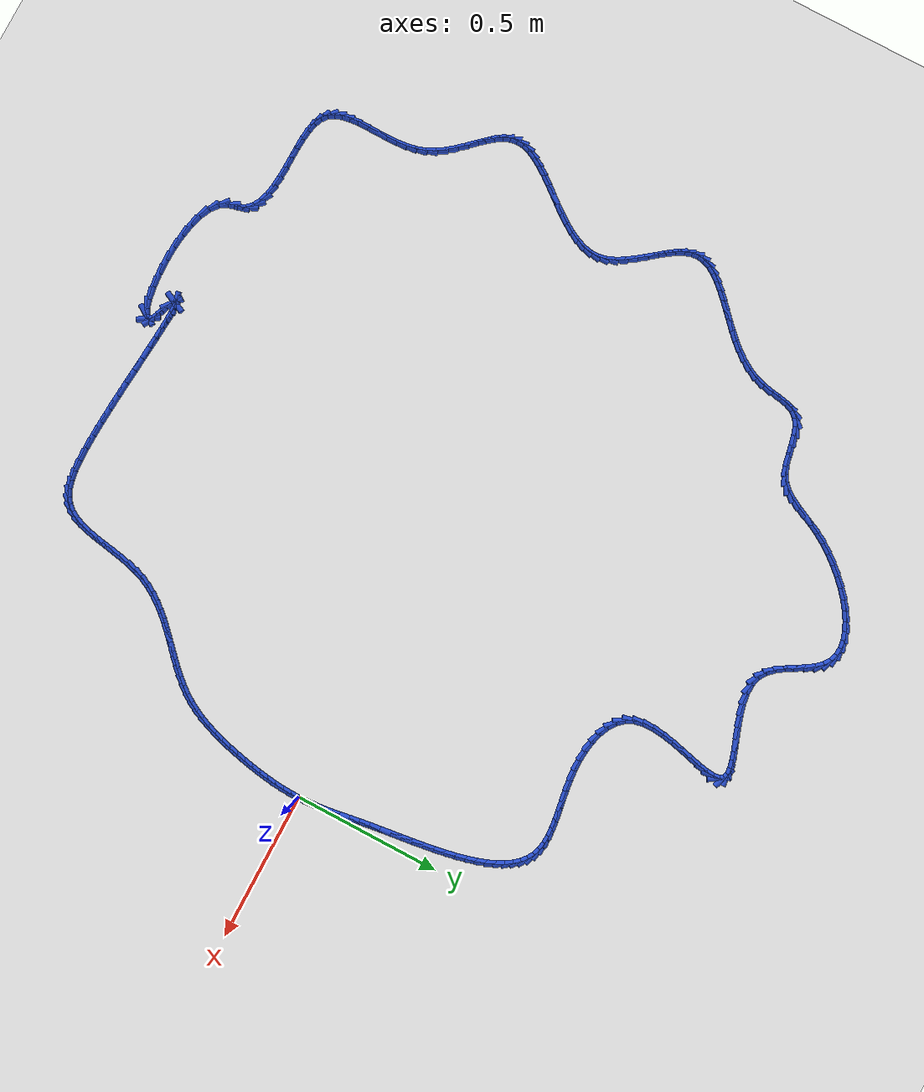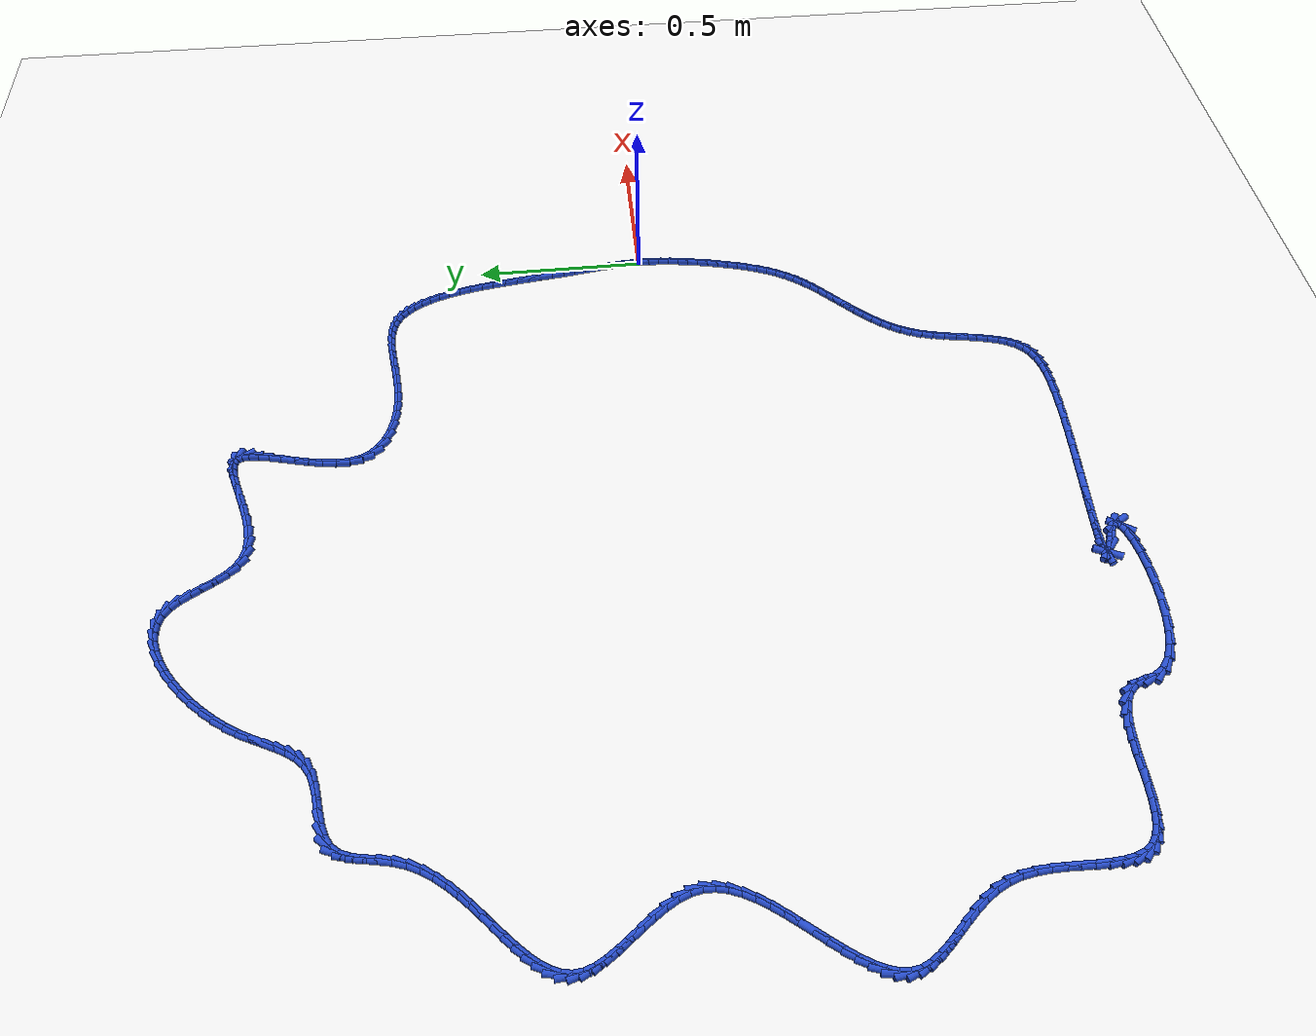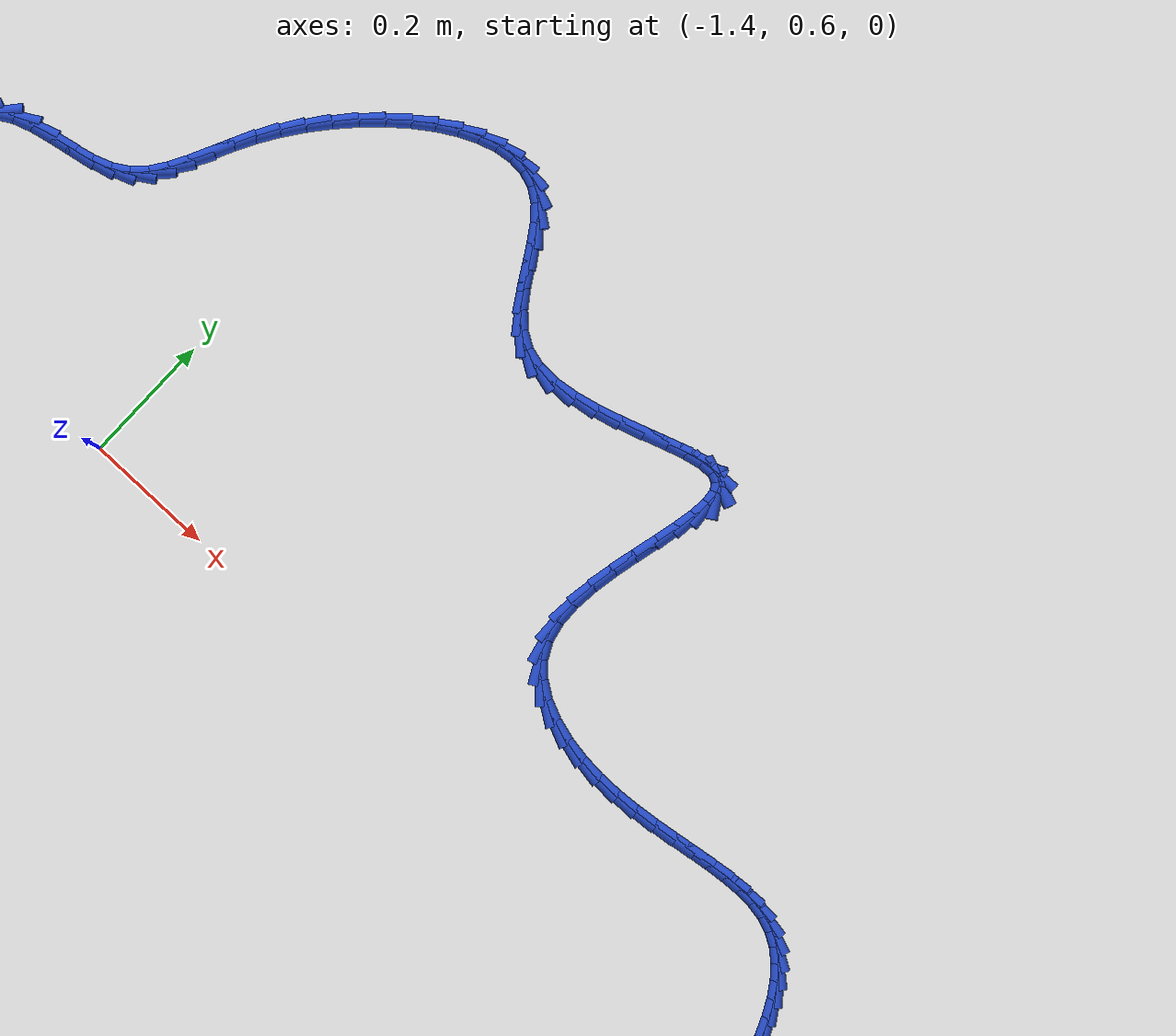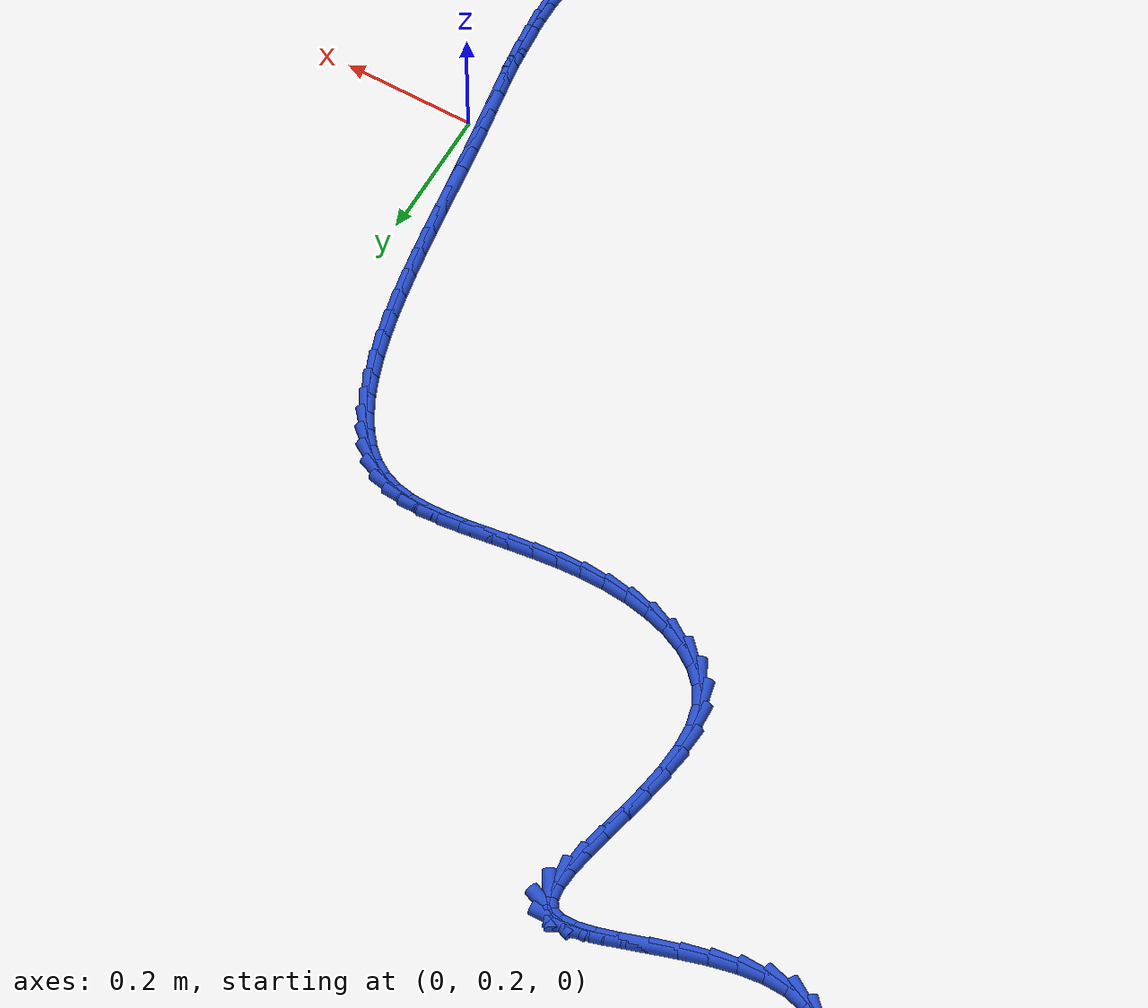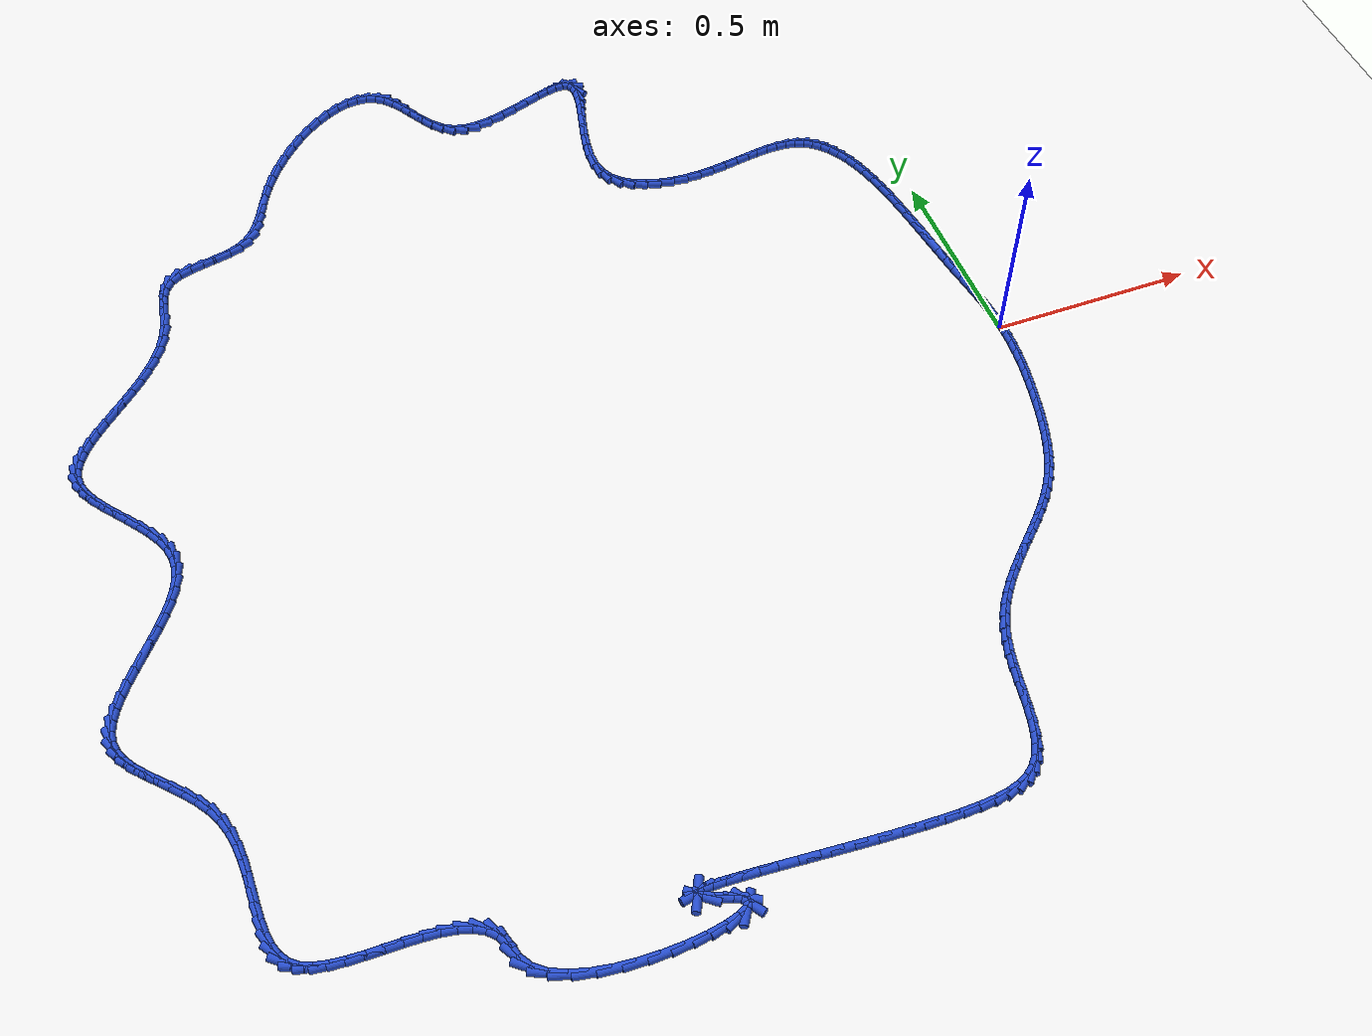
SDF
<sdf version="1.6">
 <world name="default">
  <light name="sun" type="directional">
   <pose>0 0 10 0 -0 0</pose>
   <diffuse>0.8 0.8 0.8 1</diffuse>
   <specular>0.2 0.2 0.2 1</specular>
   <attenuation>
    <range>1000</range>
    <constant>0.9</constant>
    <linear>0.01</linear>
    <quadratic>0.001</quadratic>
   </attenuation>
   <direction>-0.5 0.1 -0.9</direction>
  </light>
  <model name="ground_plane">
   <static>1</static>
   <link name="link">
    <collision name="collision">
     <geometry><plane><normal>0 0 1</normal><size>100 100</size></plane></geometry>
     <surface><friction><ode><mu>100</mu><mu2>50</mu2></ode></friction></surface>
    </collision>
    <visual name="visual">
     <cast_shadows>0</cast_shadows>
     <geometry><plane><normal>0 0 1</normal><size>100 100</size></plane></geometry>
     <material>
      <script><uri>file://media/materials/scripts/gazebo.material</uri><name>Gazebo/WhiteGlow</name></script>
     </material>
    </visual>
   </link>
  </model>
  <gravity>0 0 -9.8</gravity>
  <magnetic_field>6e-06 2.3e-05 -4.2e-05</magnetic_field>
  <atmosphere type="adiabatic"/>
  <physics name="default_physics" default="0" type="ode">
   <max_step_size>0.001</max_step_size>
   <real_time_factor>1</real_time_factor>
   <real_time_update_rate>1000</real_time_update_rate>
  </physics>
  <scene><ambient>0.4 0.4 0.4 1</ambient><background>0.7 0.7 0.7 1</background><shadows>1</shadows></scene>
  <spherical_coordinates>
   <surface_model>EARTH_WGS84</surface_model>
   <latitude_deg>0</latitude_deg>
   <longitude_deg>0</longitude_deg>
   <elevation>0</elevation>
   <heading_deg>0</heading_deg>
  </spherical_coordinates>
  <model name="line">
   <link name="link_0">
    <pose>-8.673617379884035e-19 -2.7755575615628914e-17 0.01 0 1.57 -1.5309838442177583</pose>
    <collision name="collision">
     <geometry><cylinder><radius>0.01</radius><length>0.08</length></cylinder></geometry>
    </collision>
    <visual name="visual">
     <material>
      <script><name>Gazebo/Blue</name><uri>file://media/materials/scripts/gazebo.material</uri></script>
     </material>
     <geometry><cylinder><radius>0.01</radius><length>0.08</length></cylinder></geometry>
    </visual>
   </link>
   <link name="link_1">
    <pose>-0.0011920634587532983 0.029926131072168582 0.01 0 1.57 -1.4918122423101186</pose>
    <collision name="collision">
     <geometry><cylinder><radius>0.01</radius><length>0.08</length></cylinder></geometry>
    </collision>
    <visual name="visual">
     <material>
      <script><name>Gazebo/Blue</name><uri>file://media/materials/scripts/gazebo.material</uri></script>
     </material>
     <geometry><cylinder><radius>0.01</radius><length>0.08</length></cylinder></geometry>
    </visual>
   </link>
   <link name="link_2">
    <pose>-0.0035493573256430194 0.05970921789289432 0.01 0 1.57 -1.460404947082637</pose>
    <collision name="collision">
     <geometry><cylinder><radius>0.01</radius><length>0.08</length></cylinder></geometry>
    </collision>
    <visual name="visual">
     <material>
      <script><name>Gazebo/Blue</name><uri>file://media/materials/scripts/gazebo.material</uri></script>
     </material>
     <geometry><cylinder><radius>0.01</radius><length>0.08</length></cylinder></geometry>
    </visual>
   </link>
   <link name="link_3">
    <pose>-0.006859490911630981 0.08957275082644263 0.01 0 1.57 -1.4373247160159335</pose>
    <collision name="collision">
     <geometry><cylinder><radius>0.01</radius><length>0.08</length></cylinder></geometry>
    </collision>
    <visual name="visual">
     <material>
      <script><name>Gazebo/Blue</name><uri>file://media/materials/scripts/gazebo.material</uri></script>
     </material>
     <geometry><cylinder><radius>0.01</radius><length>0.08</length></cylinder></geometry>
    </visual>
   </link>
   <link name="link_4">
    <pose>-0.010910073527679004 0.11974022023707893 0.01 0 1.57 -1.4227219335134345</pose>
    <collision name="collision">
     <geometry><cylinder><radius>0.01</radius><length>0.08</length></cylinder></geometry>
    </collision>
    <visual name="visual">
     <material>
      <script><name>Gazebo/Blue</name><uri>file://media/materials/scripts/gazebo.material</uri></script>
     </material>
     <geometry><cylinder><radius>0.01</radius><length>0.08</length></cylinder></geometry>
    </visual>
   </link>
   <link name="link_5">
    <pose>-0.015488714484748891 0.15043511648906868 0.01 0 1.57 -1.4163925502797046</pose>
    <collision name="collision">
     <geometry><cylinder><radius>0.01</radius><length>0.08</length></cylinder></geometry>
    </collision>
    <visual name="visual">
     <material>
      <script><name>Gazebo/Blue</name><uri>file://media/materials/scripts/gazebo.material</uri></script>
     </material>
     <geometry><cylinder><radius>0.01</radius><length>0.08</length></cylinder></geometry>
    </visual>
   </link>
   <link name="link_6">
    <pose>-0.020383023093802466 0.18188092994667726 0.01 0 1.57 -1.4178499350377</pose>
    <collision name="collision">
     <geometry><cylinder><radius>0.01</radius><length>0.08</length></cylinder></geometry>
    </collision>
    <visual name="visual">
     <material>
      <script><name>Gazebo/Blue</name><uri>file://media/materials/scripts/gazebo.material</uri></script>
     </material>
     <geometry><cylinder><radius>0.01</radius><length>0.08</length></cylinder></geometry>
    </visual>
   </link>
   <link name="link_7">
    <pose>-0.025380608665801545 0.2143011509741702 0.01 0 1.57 -1.4263627147588707</pose>
    <collision name="collision">
     <geometry><cylinder><radius>0.01</radius><length>0.08</length></cylinder></geometry>
    </collision>
    <visual name="visual">
     <material>
      <script><name>Gazebo/Blue</name><uri>file://media/materials/scripts/gazebo.material</uri></script>
     </material>
     <geometry><cylinder><radius>0.01</radius><length>0.08</length></cylinder></geometry>
    </visual>
   </link>
   <link name="link_8">
    <pose>-0.030270033205655977 0.24791782477390206 0.01 0 1.57 -1.4372842359377562</pose>
    <collision name="collision">
     <geometry><cylinder><radius>0.01</radius><length>0.08</length></cylinder></geometry>
    </collision>
    <visual name="visual">
     <material>
      <script><name>Gazebo/Blue</name><uri>file://media/materials/scripts/gazebo.material</uri></script>
     </material>
     <geometry><cylinder><radius>0.01</radius><length>0.08</length></cylinder></geometry>
    </visual>
   </link>
   <link name="link_9">
    <pose>-0.034952662818050914 0.2827818815865925 0.01 0 1.57 -1.4432561508847164</pose>
    <collision name="collision">
     <geometry><cylinder><radius>0.01</radius><length>0.08</length></cylinder></geometry>
    </collision>
    <visual name="visual">
     <material>
      <script><name>Gazebo/Blue</name><uri>file://media/materials/scripts/gazebo.material</uri></script>
     </material>
     <geometry><cylinder><radius>0.01</radius><length>0.08</length></cylinder></geometry>
    </visual>
   </link>
   <link name="link_10">
    <pose>-0.03954762887872493 0.3186139188363698 0.01 0 1.57 -1.443988752042576</pose>
    <collision name="collision">
     <geometry><cylinder><radius>0.01</radius><length>0.08</length></cylinder></geometry>
    </collision>
    <visual name="visual">
     <material>
      <script><name>Gazebo/Blue</name><uri>file://media/materials/scripts/gazebo.material</uri></script>
     </material>
     <geometry><cylinder><radius>0.01</radius><length>0.08</length></cylinder></geometry>
    </visual>
   </link>
   <link name="link_11">
    <pose>-0.04419889976410217 0.35509685816759995 0.01 0 1.57 -1.4397758154121778</pose>
    <collision name="collision">
     <geometry><cylinder><radius>0.01</radius><length>0.08</length></cylinder></geometry>
    </collision>
    <visual name="visual">
     <material>
      <script><name>Gazebo/Blue</name><uri>file://media/materials/scripts/gazebo.material</uri></script>
     </material>
     <geometry><cylinder><radius>0.01</radius><length>0.08</length></cylinder></geometry>
    </visual>
   </link>
   <link name="link_12">
    <pose>-0.04905044385060673 0.3919136212246486 0.01 0 1.57 -1.4306595569260248</pose>
    <collision name="collision">
     <geometry><cylinder><radius>0.01</radius><length>0.08</length></cylinder></geometry>
    </collision>
    <visual name="visual">
     <material>
      <script><name>Gazebo/Blue</name><uri>file://media/materials/scripts/gazebo.material</uri></script>
     </material>
     <geometry><cylinder><radius>0.01</radius><length>0.08</length></cylinder></geometry>
    </visual>
   </link>
   <link name="link_13">
    <pose>-0.05424622951466277 0.42874712965188194 0.01 0 1.57 -1.416449296171307</pose>
    <collision name="collision">
     <geometry><cylinder><radius>0.01</radius><length>0.08</length></cylinder></geometry>
    </collision>
    <visual name="visual">
     <material>
      <script><name>Gazebo/Blue</name><uri>file://media/materials/scripts/gazebo.material</uri></script>
     </material>
     <geometry><cylinder><radius>0.01</radius><length>0.08</length></cylinder></geometry>
    </visual>
   </link>
   <link name="link_14">
    <pose>-0.05993022513269442 0.4652803050936658 0.01 0 1.57 -1.3967155898508188</pose>
    <collision name="collision">
     <geometry><cylinder><radius>0.01</radius><length>0.08</length></cylinder></geometry>
    </collision>
    <visual name="visual">
     <material>
      <script><name>Gazebo/Blue</name><uri>file://media/materials/scripts/gazebo.material</uri></script>
     </material>
     <geometry><cylinder><radius>0.01</radius><length>0.08</length></cylinder></geometry>
    </visual>
   </link>
   <link name="link_15">
    <pose>-0.06624639908112581 0.5011960691943661 0.01 0 1.57 -1.3707615844870331</pose>
    <collision name="collision">
     <geometry><cylinder><radius>0.01</radius><length>0.08</length></cylinder></geometry>
    </collision>
    <visual name="visual">
     <material>
      <script><name>Gazebo/Blue</name><uri>file://media/materials/scripts/gazebo.material</uri></script>
     </material>
     <geometry><cylinder><radius>0.01</radius><length>0.08</length></cylinder></geometry>
    </visual>
   </link>
   <link name="link_16">
    <pose>-0.07333871973638105 0.5361773435983487 0.01 0 1.57 -1.3375707681272881</pose>
    <collision name="collision">
     <geometry><cylinder><radius>0.01</radius><length>0.08</length></cylinder></geometry>
    </collision>
    <visual name="visual">
     <material>
      <script><name>Gazebo/Blue</name><uri>file://media/materials/scripts/gazebo.material</uri></script>
     </material>
     <geometry><cylinder><radius>0.01</radius><length>0.08</length></cylinder></geometry>
    </visual>
   </link>
   <link name="link_17">
    <pose>-0.08135115547488428 0.5699070499499793 0.01 0 1.57 -1.2957294912012003</pose>
    <collision name="collision">
     <geometry><cylinder><radius>0.01</radius><length>0.08</length></cylinder></geometry>
    </collision>
    <visual name="visual">
     <material>
      <script><name>Gazebo/Blue</name><uri>file://media/materials/scripts/gazebo.material</uri></script>
     </material>
     <geometry><cylinder><radius>0.01</radius><length>0.08</length></cylinder></geometry>
    </visual>
   </link>
   <link name="link_18">
    <pose>-0.09042767467305962 0.602068109893624 0.01 0 1.57 -1.2433255833330956</pose>
    <collision name="collision">
     <geometry><cylinder><radius>0.01</radius><length>0.08</length></cylinder></geometry>
    </collision>
    <visual name="visual">
     <material>
      <script><name>Gazebo/Blue</name><uri>file://media/materials/scripts/gazebo.material</uri></script>
     </material>
     <geometry><cylinder><radius>0.01</radius><length>0.08</length></cylinder></geometry>
    </visual>
   </link>
   <link name="link_19">
    <pose>-0.10071224570733121 0.6323434450736488 0.01 0 1.57 -1.177836768705247</pose>
    <collision name="collision">
     <geometry><cylinder><radius>0.01</radius><length>0.08</length></cylinder></geometry>
    </collision>
    <visual name="visual">
     <material>
      <script><name>Gazebo/Blue</name><uri>file://media/materials/scripts/gazebo.material</uri></script>
     </material>
     <geometry><cylinder><radius>0.01</radius><length>0.08</length></cylinder></geometry>
    </visual>
   </link>
   <link name="link_20">
    <pose>-0.1123488369541232 0.6604159771344196 0.01 0 1.57 -1.0960574448967841</pose>
    <collision name="collision">
     <geometry><cylinder><radius>0.01</radius><length>0.08</length></cylinder></geometry>
    </collision>
    <visual name="visual">
     <material>
      <script><name>Gazebo/Blue</name><uri>file://media/materials/scripts/gazebo.material</uri></script>
     </material>
     <geometry><cylinder><radius>0.01</radius><length>0.08</length></cylinder></geometry>
    </visual>
   </link>
   <link name="link_21">
    <pose>-0.12548141678985966 0.685968627720302 0.01 0 1.57 -0.9941940548268737</pose>
    <collision name="collision">
     <geometry><cylinder><radius>0.01</radius><length>0.08</length></cylinder></geometry>
    </collision>
    <visual name="visual">
     <material>
      <script><name>Gazebo/Blue</name><uri>file://media/materials/scripts/gazebo.material</uri></script>
     </material>
     <geometry><cylinder><radius>0.01</radius><length>0.08</length></cylinder></geometry>
    </visual>
   </link>
   <link name="link_22">
    <pose>-0.1402539535909648 0.7086843184756622 0.01 0 1.57 -0.8684114697376889</pose>
    <collision name="collision">
     <geometry><cylinder><radius>0.01</radius><length>0.08</length></cylinder></geometry>
    </collision>
    <visual name="visual">
     <material>
      <script><name>Gazebo/Blue</name><uri>file://media/materials/scripts/gazebo.material</uri></script>
     </material>
     <geometry><cylinder><radius>0.01</radius><length>0.08</length></cylinder></geometry>
    </visual>
   </link>
   <link name="link_23">
    <pose>-0.15681041573386267 0.7282459710448659 0.01 0 1.57 -0.716272689196708</pose>
    <collision name="collision">
     <geometry><cylinder><radius>0.01</radius><length>0.08</length></cylinder></geometry>
    </collision>
    <visual name="visual">
     <material>
      <script><name>Gazebo/Blue</name><uri>file://media/materials/scripts/gazebo.material</uri></script>
     </material>
     <geometry><cylinder><radius>0.01</radius><length>0.08</length></cylinder></geometry>
    </visual>
   </link>
   <link name="link_24">
    <pose>-0.17529477159497744 0.7443365070722793 0.01 0 1.57 -0.5392959390188768</pose>
    <collision name="collision">
     <geometry><cylinder><radius>0.01</radius><length>0.08</length></cylinder></geometry>
    </collision>
    <visual name="visual">
     <material>
      <script><name>Gazebo/Blue</name><uri>file://media/materials/scripts/gazebo.material</uri></script>
     </material>
     <geometry><cylinder><radius>0.01</radius><length>0.08</length></cylinder></geometry>
    </visual>
   </link>
   <link name="link_25">
    <pose>-0.19585098955073327 0.756638848202268 0.01 0 1.57 -0.34677644705494926</pose>
    <collision name="collision">
     <geometry><cylinder><radius>0.01</radius><length>0.08</length></cylinder></geometry>
    </collision>
    <visual name="visual">
     <material>
      <script><name>Gazebo/Blue</name><uri>file://media/materials/scripts/gazebo.material</uri></script>
     </material>
     <geometry><cylinder><radius>0.01</radius><length>0.08</length></cylinder></geometry>
    </visual>
   </link>
   <link name="link_26">
    <pose>-0.21861303366019633 0.7648645888249331 0.01 0 1.57 -0.17357291917160803</pose>
    <collision name="collision">
     <geometry><cylinder><radius>0.01</radius><length>0.08</length></cylinder></geometry>
    </collision>
    <visual name="visual">
     <material>
      <script><name>Gazebo/Blue</name><uri>file://media/materials/scripts/gazebo.material</uri></script>
     </material>
     <geometry><cylinder><radius>0.01</radius><length>0.08</length></cylinder></geometry>
    </visual>
   </link>
   <link name="link_27">
    <pose>-0.24353713478854908 0.7692347132762082 0.01 0 1.57 -0.043605174973667386</pose>
    <collision name="collision">
     <geometry><cylinder><radius>0.01</radius><length>0.08</length></cylinder></geometry>
    </collision>
    <visual name="visual">
     <material>
      <script><name>Gazebo/Blue</name><uri>file://media/materials/scripts/gazebo.material</uri></script>
     </material>
     <geometry><cylinder><radius>0.01</radius><length>0.08</length></cylinder></geometry>
    </visual>
   </link>
   <link name="link_28">
    <pose>-0.2704267767794843 0.7704079845382207 0.01 0 1.57 0.04709943094118942</pose>
    <collision name="collision">
     <geometry><cylinder><radius>0.01</radius><length>0.08</length></cylinder></geometry>
    </collision>
    <visual name="visual">
     <material>
      <script><name>Gazebo/Blue</name><uri>file://media/materials/scripts/gazebo.material</uri></script>
     </material>
     <geometry><cylinder><radius>0.01</radius><length>0.08</length></cylinder></geometry>
    </visual>
   </link>
   <link name="link_29">
    <pose>-0.2990804723767562 0.7690574129504607 0.01 0 1.57 0.10555591531187349</pose>
    <collision name="collision">
     <geometry><cylinder><radius>0.01</radius><length>0.08</length></cylinder></geometry>
    </collision>
    <visual name="visual">
     <material>
      <script><name>Gazebo/Blue</name><uri>file://media/materials/scripts/gazebo.material</uri></script>
     </material>
     <geometry><cylinder><radius>0.01</radius><length>0.08</length></cylinder></geometry>
    </visual>
   </link>
   <link name="link_30">
    <pose>-0.32929673432411916 0.7658560088524181 0.01 0 1.57 0.13780358688289648</pose>
    <collision name="collision">
     <geometry><cylinder><radius>0.01</radius><length>0.08</length></cylinder></geometry>
    </collision>
    <visual name="visual">
     <material>
      <script><name>Gazebo/Blue</name><uri>file://media/materials/scripts/gazebo.material</uri></script>
     </material>
     <geometry><cylinder><radius>0.01</radius><length>0.08</length></cylinder></geometry>
    </visual>
   </link>
   <link name="link_31">
    <pose>-0.36087407536532773 0.7614767825835832 0.01 0 1.57 0.14809812832370803</pose>
    <collision name="collision">
     <geometry><cylinder><radius>0.01</radius><length>0.08</length></cylinder></geometry>
    </collision>
    <visual name="visual">
     <material>
      <script><name>Gazebo/Blue</name><uri>file://media/materials/scripts/gazebo.material</uri></script>
     </material>
     <geometry><cylinder><radius>0.01</radius><length>0.08</length></cylinder></geometry>
    </visual>
   </link>
   <link name="link_32">
    <pose>-0.393611008244136 0.7565927444834457 0.01 0 1.57 0.1390532798144031</pose>
    <collision name="collision">
     <geometry><cylinder><radius>0.01</radius><length>0.08</length></cylinder></geometry>
    </collision>
    <visual name="visual">
     <material>
      <script><name>Gazebo/Blue</name><uri>file://media/materials/scripts/gazebo.material</uri></script>
     </material>
     <geometry><cylinder><radius>0.01</radius><length>0.08</length></cylinder></geometry>
    </visual>
   </link>
   <link name="link_33">
    <pose>-0.4273060457042981 0.7518769048914955 0.01 0 1.57 0.11199512746065339</pose>
    <collision name="collision">
     <geometry><cylinder><radius>0.01</radius><length>0.08</length></cylinder></geometry>
    </collision>
    <visual name="visual">
     <material>
      <script><name>Gazebo/Blue</name><uri>file://media/materials/scripts/gazebo.material</uri></script>
     </material>
     <geometry><cylinder><radius>0.01</radius><length>0.08</length></cylinder></geometry>
    </visual>
   </link>
   <link name="link_34">
    <pose>-0.4617577004895692 0.748002274147223 0.01 0 1.57 0.06732535251456545</pose>
    <collision name="collision">
     <geometry><cylinder><radius>0.01</radius><length>0.08</length></cylinder></geometry>
    </collision>
    <visual name="visual">
     <material>
      <script><name>Gazebo/Blue</name><uri>file://media/materials/scripts/gazebo.material</uri></script>
     </material>
     <geometry><cylinder><radius>0.01</radius><length>0.08</length></cylinder></geometry>
    </visual>
   </link>
   <link name="link_35">
    <pose>-0.4967644853437031 0.7456418625901178 0.01 0 1.57 0.004897583462820806</pose>
    <collision name="collision">
     <geometry><cylinder><radius>0.01</radius><length>0.08</length></cylinder></geometry>
    </collision>
    <visual name="visual">
     <material>
      <script><name>Gazebo/Blue</name><uri>file://media/materials/scripts/gazebo.material</uri></script>
     </material>
     <geometry><cylinder><radius>0.01</radius><length>0.08</length></cylinder></geometry>
    </visual>
   </link>
   <link name="link_36">
    <pose>-0.532124913010454 0.7454686805596699 0.01 0 1.57 -0.0751768790568628</pose>
    <collision name="collision">
     <geometry><cylinder><radius>0.01</radius><length>0.08</length></cylinder></geometry>
    </collision>
    <visual name="visual">
     <material>
      <script><name>Gazebo/Blue</name><uri>file://media/materials/scripts/gazebo.material</uri></script>
     </material>
     <geometry><cylinder><radius>0.01</radius><length>0.08</length></cylinder></geometry>
    </visual>
   </link>
   <link name="link_37">
    <pose>-0.5676006343412286 0.7481406701083774 0.01 0 1.57 -0.16946726879782714</pose>
    <collision name="collision">
     <geometry><cylinder><radius>0.01</radius><length>0.08</length></cylinder></geometry>
    </collision>
    <visual name="visual">
     <material>
      <script><name>Gazebo/Blue</name><uri>file://media/materials/scripts/gazebo.material</uri></script>
     </material>
     <geometry><cylinder><radius>0.01</radius><length>0.08</length></cylinder></geometry>
    </visual>
   </link>
   <link name="link_38">
    <pose>-0.6024233030745086 0.7540991227563392 0.01 0 1.57 -0.2809337188770969</pose>
    <collision name="collision">
     <geometry><cylinder><radius>0.01</radius><length>0.08</length></cylinder></geometry>
    </collision>
    <visual name="visual">
     <material>
      <script><name>Gazebo/Blue</name><uri>file://media/materials/scripts/gazebo.material</uri></script>
     </material>
     <geometry><cylinder><radius>0.01</radius><length>0.08</length></cylinder></geometry>
    </visual>
   </link>
   <link name="link_39">
    <pose>-0.6354273361624305 0.7636229488348666 0.01 0 1.57 -0.41895626845242995</pose>
    <collision name="collision">
     <geometry><cylinder><radius>0.01</radius><length>0.08</length></cylinder></geometry>
    </collision>
    <visual name="visual">
     <material>
      <script><name>Gazebo/Blue</name><uri>file://media/materials/scripts/gazebo.material</uri></script>
     </material>
     <geometry><cylinder><radius>0.01</radius><length>0.08</length></cylinder></geometry>
    </visual>
   </link>
   <link name="link_40">
    <pose>-0.665437534666611 0.7769871279221601 0.01 0 1.57 -0.5947253696957779</pose>
    <collision name="collision">
     <geometry><cylinder><radius>0.01</radius><length>0.08</length></cylinder></geometry>
    </collision>
    <visual name="visual">
     <material>
      <script><name>Gazebo/Blue</name><uri>file://media/materials/scripts/gazebo.material</uri></script>
     </material>
     <geometry><cylinder><radius>0.01</radius><length>0.08</length></cylinder></geometry>
    </visual>
   </link>
   <link name="link_41">
    <pose>-0.6912786996486677 0.7944666395964205 0.01 0 1.57 -0.8177917471947918</pose>
    <collision name="collision">
     <geometry><cylinder><radius>0.01</radius><length>0.08</length></cylinder></geometry>
    </collision>
    <visual name="visual">
     <material>
      <script><name>Gazebo/Blue</name><uri>file://media/materials/scripts/gazebo.material</uri></script>
     </material>
     <geometry><cylinder><radius>0.01</radius><length>0.08</length></cylinder></geometry>
    </visual>
   </link>
   <link name="link_42">
    <pose>-0.7117756321702178 0.8163364634358485 0.01 0 1.57 -1.0858686030148896</pose>
    <collision name="collision">
     <geometry><cylinder><radius>0.01</radius><length>0.08</length></cylinder></geometry>
    </collision>
    <visual name="visual">
     <material>
      <script><name>Gazebo/Blue</name><uri>file://media/materials/scripts/gazebo.material</uri></script>
     </material>
     <geometry><cylinder><radius>0.01</radius><length>0.08</length></cylinder></geometry>
    </visual>
   </link>
   <link name="link_43">
    <pose>-0.7257558929972162 0.842869994935702 0.01 0 1.57 -1.349795668924358</pose>
    <collision name="collision">
     <geometry><cylinder><radius>0.01</radius><length>0.08</length></cylinder></geometry>
    </collision>
    <visual name="visual">
     <material>
      <script><name>Gazebo/Blue</name><uri>file://media/materials/scripts/gazebo.material</uri></script>
     </material>
     <geometry><cylinder><radius>0.01</radius><length>0.08</length></cylinder></geometry>
    </visual>
   </link>
   <link name="link_44">
    <pose>-0.7327373839717425 0.8739443706485378 0.01 0 1.57 -1.5391064750870342</pose>
    <collision name="collision">
     <geometry><cylinder><radius>0.01</radius><length>0.08</length></cylinder></geometry>
    </collision>
    <visual name="visual">
     <material>
      <script><name>Gazebo/Blue</name><uri>file://media/materials/scripts/gazebo.material</uri></script>
     </material>
     <geometry><cylinder><radius>0.01</radius><length>0.08</length></cylinder></geometry>
    </visual>
   </link>
   <link name="link_45">
    <pose>-0.7338334766400432 0.9085209202019734 0.01 0 1.57 1.4775661834523324</pose>
    <collision name="collision">
     <geometry><cylinder><radius>0.01</radius><length>0.08</length></cylinder></geometry>
    </collision>
    <visual name="visual">
     <material>
      <script><name>Gazebo/Blue</name><uri>file://media/materials/scripts/gazebo.material</uri></script>
     </material>
     <geometry><cylinder><radius>0.01</radius><length>0.08</length></cylinder></geometry>
    </visual>
   </link>
   <link name="link_46">
    <pose>-0.7303822471487614 0.9454319917527966 0.01 0 1.57 1.3976312926035983</pose>
    <collision name="collision">
     <geometry><cylinder><radius>0.01</radius><length>0.08</length></cylinder></geometry>
    </collision>
    <visual name="visual">
     <material>
      <script><name>Gazebo/Blue</name><uri>file://media/materials/scripts/gazebo.material</uri></script>
     </material>
     <geometry><cylinder><radius>0.01</radius><length>0.08</length></cylinder></geometry>
    </visual>
   </link>
   <link name="link_47">
    <pose>-0.7237217716445401 0.9835099334577941 0.01 0 1.57 1.3503748469150667</pose>
    <collision name="collision">
     <geometry><cylinder><radius>0.01</radius><length>0.08</length></cylinder></geometry>
    </collision>
    <visual name="visual">
     <material>
      <script><name>Gazebo/Blue</name><uri>file://media/materials/scripts/gazebo.material</uri></script>
     </material>
     <geometry><cylinder><radius>0.01</radius><length>0.08</length></cylinder></geometry>
    </visual>
   </link>
   <link name="link_48">
    <pose>-0.7151901262740218 1.0215870934737539 0.01 0 1.57 1.329964235913607</pose>
    <collision name="collision">
     <geometry><cylinder><radius>0.01</radius><length>0.08</length></cylinder></geometry>
    </collision>
    <visual name="visual">
     <material>
      <script><name>Gazebo/Blue</name><uri>file://media/materials/scripts/gazebo.material</uri></script>
     </material>
     <geometry><cylinder><radius>0.01</radius><length>0.08</length></cylinder></geometry>
    </visual>
   </link>
   <link name="link_49">
    <pose>-0.7061253871838494 1.0584958199574621 0.01 0 1.57 1.3362820452198823</pose>
    <collision name="collision">
     <geometry><cylinder><radius>0.01</radius><length>0.08</length></cylinder></geometry>
    </collision>
    <visual name="visual">
     <material>
      <script><name>Gazebo/Blue</name><uri>file://media/materials/scripts/gazebo.material</uri></script>
     </material>
     <geometry><cylinder><radius>0.01</radius><length>0.08</length></cylinder></geometry>
    </visual>
   </link>
   <link name="link_50">
    <pose>-0.6978656305206656 1.0930684610657073 0.01 0 1.57 1.3764071358228145</pose>
    <collision name="collision">
     <geometry><cylinder><radius>0.01</radius><length>0.08</length></cylinder></geometry>
    </collision>
    <visual name="visual">
     <material>
      <script><name>Gazebo/Blue</name><uri>file://media/materials/scripts/gazebo.material</uri></script>
     </material>
     <geometry><cylinder><radius>0.01</radius><length>0.08</length></cylinder></geometry>
    </visual>
   </link>
   <link name="link_51">
    <pose>-0.6917489324311131 1.1241373649552766 0.01 0 1.57 1.4712847615201314</pose>
    <collision name="collision">
     <geometry><cylinder><radius>0.01</radius><length>0.08</length></cylinder></geometry>
    </collision>
    <visual name="visual">
     <material>
      <script><name>Gazebo/Blue</name><uri>file://media/materials/scripts/gazebo.material</uri></script>
     </material>
     <geometry><cylinder><radius>0.01</radius><length>0.08</length></cylinder></geometry>
    </visual>
   </link>
   <link name="link_52">
    <pose>-0.689113369061835 1.1505348797829569 0.01 0 1.57 -1.4649766666540844</pose>
    <collision name="collision">
     <geometry><cylinder><radius>0.01</radius><length>0.08</length></cylinder></geometry>
    </collision>
    <visual name="visual">
     <material>
      <script><name>Gazebo/Blue</name><uri>file://media/materials/scripts/gazebo.material</uri></script>
     </material>
     <geometry><cylinder><radius>0.01</radius><length>0.08</length></cylinder></geometry>
    </visual>
   </link>
   <link name="link_53">
    <pose>-0.6912970165594738 1.1710933537055352 0.01 0 1.57 -1.0190676660068214</pose>
    <collision name="collision">
     <geometry><cylinder><radius>0.01</radius><length>0.08</length></cylinder></geometry>
    </collision>
    <visual name="visual">
     <material>
      <script><name>Gazebo/Blue</name><uri>file://media/materials/scripts/gazebo.material</uri></script>
     </material>
     <geometry><cylinder><radius>0.01</radius><length>0.08</length></cylinder></geometry>
    </visual>
   </link>
   <link name="link_54">
    <pose>-0.6996379509443508 1.1846451350189793 0.01 0 1.57 -0.36168302062955593</pose>
    <collision name="collision">
     <geometry><cylinder><radius>0.01</radius><length>0.08</length></cylinder></geometry>
    </collision>
    <visual name="visual">
     <material>
      <script><name>Gazebo/Blue</name><uri>file://media/materials/scripts/gazebo.material</uri></script>
     </material>
     <geometry><cylinder><radius>0.01</radius><length>0.08</length></cylinder></geometry>
    </visual>
   </link>
   <link name="link_55">
    <pose>-0.7150595227192715 1.1904795095031495 0.01 0 1.57 0.0368072957396625</pose>
    <collision name="collision">
     <geometry><cylinder><radius>0.01</radius><length>0.08</length></cylinder></geometry>
    </collision>
    <visual name="visual">
     <material>
      <script><name>Gazebo/Blue</name><uri>file://media/materials/scripts/gazebo.material</uri></script>
     </material>
     <geometry><cylinder><radius>0.01</radius><length>0.08</length></cylinder></geometry>
    </visual>
   </link>
   <link name="link_56">
    <pose>-0.7368595498400109 1.1896767469035965 0.01 0 1.57 0.21527165208525095</pose>
    <collision name="collision">
     <geometry><cylinder><radius>0.01</radius><length>0.08</length></cylinder></geometry>
    </collision>
    <visual name="visual">
     <material>
      <script><name>Gazebo/Blue</name><uri>file://media/materials/scripts/gazebo.material</uri></script>
     </material>
     <geometry><cylinder><radius>0.01</radius><length>0.08</length></cylinder></geometry>
    </visual>
   </link>
   <link name="link_57">
    <pose>-0.7639376423660004 1.1837558556171897 0.01 0 1.57 0.29565711391072097</pose>
    <collision name="collision">
     <geometry><cylinder><radius>0.01</radius><length>0.08</length></cylinder></geometry>
    </collision>
    <visual name="visual">
     <material>
      <script><name>Gazebo/Blue</name><uri>file://media/materials/scripts/gazebo.material</uri></script>
     </material>
     <geometry><cylinder><radius>0.01</radius><length>0.08</length></cylinder></geometry>
    </visual>
   </link>
   <link name="link_58">
    <pose>-0.7951934103566707 1.1742358440407985 0.01 0 1.57 0.3258283661167217</pose>
    <collision name="collision">
     <geometry><cylinder><radius>0.01</radius><length>0.08</length></cylinder></geometry>
    </collision>
    <visual name="visual">
     <material>
      <script><name>Gazebo/Blue</name><uri>file://media/materials/scripts/gazebo.material</uri></script>
     </material>
     <geometry><cylinder><radius>0.01</radius><length>0.08</length></cylinder></geometry>
    </visual>
   </link>
   <link name="link_59">
    <pose>-0.8295264638714522 1.1626357205712932 0.01 0 1.57 0.32318527351842097</pose>
    <collision name="collision">
     <geometry><cylinder><radius>0.01</radius><length>0.08</length></cylinder></geometry>
    </collision>
    <visual name="visual">
     <material>
      <script><name>Gazebo/Blue</name><uri>file://media/materials/scripts/gazebo.material</uri></script>
     </material>
     <geometry><cylinder><radius>0.01</radius><length>0.08</length></cylinder></geometry>
    </visual>
   </link>
   <link name="link_60">
    <pose>-0.8658364129697762 1.1504744936055442 0.01 0 1.57 0.29262544058438467</pose>
    <collision name="collision">
     <geometry><cylinder><radius>0.01</radius><length>0.08</length></cylinder></geometry>
    </collision>
    <visual name="visual">
     <material>
      <script><name>Gazebo/Blue</name><uri>file://media/materials/scripts/gazebo.material</uri></script>
     </material>
     <geometry><cylinder><radius>0.01</radius><length>0.08</length></cylinder></geometry>
    </visual>
   </link>
   <link name="link_61">
    <pose>-0.9030228677110735 1.139271171540421 0.01 0 1.57 0.23184249930451575</pose>
    <collision name="collision">
     <geometry><cylinder><radius>0.01</radius><length>0.08</length></cylinder></geometry>
    </collision>
    <visual name="visual">
     <material>
      <script><name>Gazebo/Blue</name><uri>file://media/materials/scripts/gazebo.material</uri></script>
     </material>
     <geometry><cylinder><radius>0.01</radius><length>0.08</length></cylinder></geometry>
    </visual>
   </link>
   <link name="link_62">
    <pose>-0.9399854381547748 1.1305447627727925 0.01 0 1.57 0.13196464720542928</pose>
    <collision name="collision">
     <geometry><cylinder><radius>0.01</radius><length>0.08</length></cylinder></geometry>
    </collision>
    <visual name="visual">
     <material>
      <script><name>Gazebo/Blue</name><uri>file://media/materials/scripts/gazebo.material</uri></script>
     </material>
     <geometry><cylinder><radius>0.01</radius><length>0.08</length></cylinder></geometry>
    </visual>
   </link>
   <link name="link_63">
    <pose>-0.9756237343603114 1.1258142756995302 0.01 0 1.57 -0.023613714036213106</pose>
    <collision name="collision">
     <geometry><cylinder><radius>0.01</radius><length>0.08</length></cylinder></geometry>
    </collision>
    <visual name="visual">
     <material>
      <script><name>Gazebo/Blue</name><uri>file://media/materials/scripts/gazebo.material</uri></script>
     </material>
     <geometry><cylinder><radius>0.01</radius><length>0.08</length></cylinder></geometry>
    </visual>
   </link>
   <link name="link_64">
    <pose>-1.0088373663871133 1.126598718717503 0.01 0 1.57 -0.2575000470416673</pose>
    <collision name="collision">
     <geometry><cylinder><radius>0.01</radius><length>0.08</length></cylinder></geometry>
    </collision>
    <visual name="visual">
     <material>
      <script><name>Gazebo/Blue</name><uri>file://media/materials/scripts/gazebo.material</uri></script>
     </material>
     <geometry><cylinder><radius>0.01</radius><length>0.08</length></cylinder></geometry>
    </visual>
   </link>
   <link name="link_65">
    <pose>-1.0385259442946118 1.1344171002235808 0.01 0 1.57 -0.5570299091420484</pose>
    <collision name="collision">
     <geometry><cylinder><radius>0.01</radius><length>0.08</length></cylinder></geometry>
    </collision>
    <visual name="visual">
     <material>
      <script><name>Gazebo/Blue</name><uri>file://media/materials/scripts/gazebo.material</uri></script>
     </material>
     <geometry><cylinder><radius>0.01</radius><length>0.08</length></cylinder></geometry>
    </visual>
   </link>
   <link name="link_66">
    <pose>-1.0639125861375751 1.1502284004064944 0.01 0 1.57 -0.7981371832090325</pose>
    <collision name="collision">
     <geometry><cylinder><radius>0.01</radius><length>0.08</length></cylinder></geometry>
    </collision>
    <visual name="visual">
     <material>
      <script><name>Gazebo/Blue</name><uri>file://media/materials/scripts/gazebo.material</uri></script>
     </material>
     <geometry><cylinder><radius>0.01</radius><length>0.08</length></cylinder></geometry>
    </visual>
   </link>
   <link name="link_67">
    <pose>-1.085646373729949 1.1725230980873538 0.01 0 1.57 -0.947294685701872</pose>
    <collision name="collision">
     <geometry><cylinder><radius>0.01</radius><length>0.08</length></cylinder></geometry>
    </collision>
    <visual name="visual">
     <material>
      <script><name>Gazebo/Blue</name><uri>file://media/materials/scripts/gazebo.material</uri></script>
     </material>
     <geometry><cylinder><radius>0.01</radius><length>0.08</length></cylinder></geometry>
    </visual>
   </link>
   <link name="link_68">
    <pose>-1.1047691575569256 1.1991117459700105 0.01 0 1.57 -1.0217661538840968</pose>
    <collision name="collision">
     <geometry><cylinder><radius>0.01</radius><length>0.08</length></cylinder></geometry>
    </collision>
    <visual name="visual">
     <material>
      <script><name>Gazebo/Blue</name><uri>file://media/materials/scripts/gazebo.material</uri></script>
     </material>
     <geometry><cylinder><radius>0.01</radius><length>0.08</length></cylinder></geometry>
    </visual>
   </link>
   <link name="link_69">
    <pose>-1.1223228001824475 1.2278048758486622 0.01 0 1.57 -1.0339447680257958</pose>
    <collision name="collision">
     <geometry><cylinder><radius>0.01</radius><length>0.08</length></cylinder></geometry>
    </collision>
    <visual name="visual">
     <material>
      <script><name>Gazebo/Blue</name><uri>file://media/materials/scripts/gazebo.material</uri></script>
     </material>
     <geometry><cylinder><radius>0.01</radius><length>0.08</length></cylinder></geometry>
    </visual>
   </link>
   <link name="link_70">
    <pose>-1.139349164170456 1.256413019517506 0.01 0 1.57 -0.9831840949513274</pose>
    <collision name="collision">
     <geometry><cylinder><radius>0.01</radius><length>0.08</length></cylinder></geometry>
    </collision>
    <visual name="visual">
     <material>
      <script><name>Gazebo/Blue</name><uri>file://media/materials/scripts/gazebo.material</uri></script>
     </material>
     <geometry><cylinder><radius>0.01</radius><length>0.08</length></cylinder></geometry>
    </visual>
   </link>
   <link name="link_71">
    <pose>-1.1568901120848927 1.2827467087707387 0.01 0 1.57 -0.8529681778314206</pose>
    <collision name="collision">
     <geometry><cylinder><radius>0.01</radius><length>0.08</length></cylinder></geometry>
    </collision>
    <visual name="visual">
     <material>
      <script><name>Gazebo/Blue</name><uri>file://media/materials/scripts/gazebo.material</uri></script>
     </material>
     <geometry><cylinder><radius>0.01</radius><length>0.08</length></cylinder></geometry>
    </visual>
   </link>
   <link name="link_72">
    <pose>-1.1759875064897007 1.3046164754025587 0.01 0 1.57 -0.6192459355643442</pose>
    <collision name="collision">
     <geometry><cylinder><radius>0.01</radius><length>0.08</length></cylinder></geometry>
    </collision>
    <visual name="visual">
     <material>
      <script><name>Gazebo/Blue</name><uri>file://media/materials/scripts/gazebo.material</uri></script>
     </material>
     <geometry><cylinder><radius>0.01</radius><length>0.08</length></cylinder></geometry>
    </visual>
   </link>
   <link name="link_73">
    <pose>-1.1975858368351269 1.3200111439633708 0.01 0 1.57 -0.3404955863911096</pose>
    <collision name="collision">
     <geometry><cylinder><radius>0.01</radius><length>0.08</length></cylinder></geometry>
    </collision>
    <visual name="visual">
     <material>
      <script><name>Gazebo/Blue</name><uri>file://media/materials/scripts/gazebo.material</uri></script>
     </material>
     <geometry><cylinder><radius>0.01</radius><length>0.08</length></cylinder></geometry>
    </visual>
   </link>
   <link name="link_74">
    <pose>-1.221730652946045 1.3285655213224539 0.01 0 1.57 -0.08504919665741796</pose>
    <collision name="collision">
     <geometry><cylinder><radius>0.01</radius><length>0.08</length></cylinder></geometry>
    </collision>
    <visual name="visual">
     <material>
      <script><name>Gazebo/Blue</name><uri>file://media/materials/scripts/gazebo.material</uri></script>
     </material>
     <geometry><cylinder><radius>0.01</radius><length>0.08</length></cylinder></geometry>
    </visual>
   </link>
   <link name="link_75">
    <pose>-1.247981900912136 1.3308035676798982 0.01 0 1.57 0.12634848457698927</pose>
    <collision name="collision">
     <geometry><cylinder><radius>0.01</radius><length>0.08</length></cylinder></geometry>
    </collision>
    <visual name="visual">
     <material>
      <script><name>Gazebo/Blue</name><uri>file://media/materials/scripts/gazebo.material</uri></script>
     </material>
     <geometry><cylinder><radius>0.01</radius><length>0.08</length></cylinder></geometry>
    </visual>
   </link>
   <link name="link_76">
    <pose>-1.2758947827266114 1.3272579298023763 0.01 0 1.57 0.29327493461313775</pose>
    <collision name="collision">
     <geometry><cylinder><radius>0.01</radius><length>0.08</length></cylinder></geometry>
    </collision>
    <visual name="visual">
     <material>
      <script><name>Gazebo/Blue</name><uri>file://media/materials/scripts/gazebo.material</uri></script>
     </material>
     <geometry><cylinder><radius>0.01</radius><length>0.08</length></cylinder></geometry>
    </visual>
   </link>
   <link name="link_77">
    <pose>-1.305024500382684 1.3184612544565595 0.01 0 1.57 0.4245012357309593</pose>
    <collision name="collision">
     <geometry><cylinder><radius>0.01</radius><length>0.08</length></cylinder></geometry>
    </collision>
    <visual name="visual">
     <material>
      <script><name>Gazebo/Blue</name><uri>file://media/materials/scripts/gazebo.material</uri></script>
     </material>
     <geometry><cylinder><radius>0.01</radius><length>0.08</length></cylinder></geometry>
    </visual>
   </link>
   <link name="link_78">
    <pose>-1.3349262558735653 1.3049461884091194 0.01 0 1.57 0.5297322021029683</pose>
    <collision name="collision">
     <geometry><cylinder><radius>0.01</radius><length>0.08</length></cylinder></geometry>
    </collision>
    <visual name="visual">
     <material>
      <script><name>Gazebo/Blue</name><uri>file://media/materials/scripts/gazebo.material</uri></script>
     </material>
     <geometry><cylinder><radius>0.01</radius><length>0.08</length></cylinder></geometry>
    </visual>
   </link>
   <link name="link_79">
    <pose>-1.3651552511924674 1.2872453784267284 0.01 0 1.57 0.6168489731235464</pose>
    <collision name="collision">
     <geometry><cylinder><radius>0.01</radius><length>0.08</length></cylinder></geometry>
    </collision>
    <visual name="visual">
     <material>
      <script><name>Gazebo/Blue</name><uri>file://media/materials/scripts/gazebo.material</uri></script>
     </material>
     <geometry><cylinder><radius>0.01</radius><length>0.08</length></cylinder></geometry>
    </visual>
   </link>
   <link name="link_80">
    <pose>-1.395266688332602 1.2658914712760576 0.01 0 1.57 0.6917374154410754</pose>
    <collision name="collision">
     <geometry><cylinder><radius>0.01</radius><length>0.08</length></cylinder></geometry>
    </collision>
    <visual name="visual">
     <material>
      <script><name>Gazebo/Blue</name><uri>file://media/materials/scripts/gazebo.material</uri></script>
     </material>
     <geometry><cylinder><radius>0.01</radius><length>0.08</length></cylinder></geometry>
    </visual>
   </link>
   <link name="link_81">
    <pose>-1.4248157692871815 1.241417113723779 0.01 0 1.57 0.7587919112067915</pose>
    <collision name="collision">
     <geometry><cylinder><radius>0.01</radius><length>0.08</length></cylinder></geometry>
    </collision>
    <visual name="visual">
     <material>
      <script><name>Gazebo/Blue</name><uri>file://media/materials/scripts/gazebo.material</uri></script>
     </material>
     <geometry><cylinder><radius>0.01</radius><length>0.08</length></cylinder></geometry>
    </visual>
   </link>
   <link name="link_82">
    <pose>-1.4533576960494177 1.2143549525365644 0.01 0 1.57 0.8214515811731434</pose>
    <collision name="collision">
     <geometry><cylinder><radius>0.01</radius><length>0.08</length></cylinder></geometry>
    </collision>
    <visual name="visual">
     <material>
      <script><name>Gazebo/Blue</name><uri>file://media/materials/scripts/gazebo.material</uri></script>
     </material>
     <geometry><cylinder><radius>0.01</radius><length>0.08</length></cylinder></geometry>
    </visual>
   </link>
   <link name="link_83">
    <pose>-1.4804476706125231 1.1852376344810853 0.01 0 1.57 0.8826420778739458</pose>
    <collision name="collision">
     <geometry><cylinder><radius>0.01</radius><length>0.08</length></cylinder></geometry>
    </collision>
    <visual name="visual">
     <material>
      <script><name>Gazebo/Blue</name><uri>file://media/materials/scripts/gazebo.material</uri></script>
     </material>
     <geometry><cylinder><radius>0.01</radius><length>0.08</length></cylinder></geometry>
    </visual>
   </link>
   <link name="link_84">
    <pose>-1.505640894969709 1.1545978063240137 0.01 0 1.57 0.9451448736222566</pose>
    <collision name="collision">
     <geometry><cylinder><radius>0.01</radius><length>0.08</length></cylinder></geometry>
    </collision>
    <visual name="visual">
     <material>
      <script><name>Gazebo/Blue</name><uri>file://media/materials/scripts/gazebo.material</uri></script>
     </material>
     <geometry><cylinder><radius>0.01</radius><length>0.08</length></cylinder></geometry>
    </visual>
   </link>
   <link name="link_85">
    <pose>-1.5284925711141875 1.1229681148320214 0.01 0 1.57 1.0119502504168083</pose>
    <collision name="collision">
     <geometry><cylinder><radius>0.01</radius><length>0.08</length></cylinder></geometry>
    </collision>
    <visual name="visual">
     <material>
      <script><name>Gazebo/Blue</name><uri>file://media/materials/scripts/gazebo.material</uri></script>
     </material>
     <geometry><cylinder><radius>0.01</radius><length>0.08</length></cylinder></geometry>
    </visual>
   </link>
   <link name="link_86">
    <pose>-1.5485579010391712 1.0908812067717797 0.01 0 1.57 1.0805561548901128</pose>
    <collision name="collision">
     <geometry><cylinder><radius>0.01</radius><length>0.08</length></cylinder></geometry>
    </collision>
    <visual name="visual">
     <material>
      <script><name>Gazebo/Blue</name><uri>file://media/materials/scripts/gazebo.material</uri></script>
     </material>
     <geometry><cylinder><radius>0.01</radius><length>0.08</length></cylinder></geometry>
    </visual>
   </link>
   <link name="link_87">
    <pose>-1.5656249235765292 1.0589023263864956 0.01 0 1.57 1.1213152404434834</pose>
    <collision name="collision">
     <geometry><cylinder><radius>0.01</radius><length>0.08</length></cylinder></geometry>
    </collision>
    <visual name="visual">
     <material>
      <script><name>Gazebo/Blue</name><uri>file://media/materials/scripts/gazebo.material</uri></script>
     </material>
     <geometry><cylinder><radius>0.01</radius><length>0.08</length></cylinder></geometry>
    </visual>
   </link>
   <link name="link_88">
    <pose>-1.5806484250973594 1.0277600641739928 0.01 0 1.57 1.119786827306552</pose>
    <collision name="collision">
     <geometry><cylinder><radius>0.01</radius><length>0.08</length></cylinder></geometry>
    </collision>
    <visual name="visual">
     <material>
      <script><name>Gazebo/Blue</name><uri>file://media/materials/scripts/gazebo.material</uri></script>
     </material>
     <geometry><cylinder><radius>0.01</radius><length>0.08</length></cylinder></geometry>
    </visual>
   </link>
   <link name="link_89">
    <pose>-1.5949478864759667 0.9982340683623879 0.01 0 1.57 1.0687036214663233</pose>
    <collision name="collision">
     <geometry><cylinder><radius>0.01</radius><length>0.08</length></cylinder></geometry>
    </collision>
    <visual name="visual">
     <material>
      <script><name>Gazebo/Blue</name><uri>file://media/materials/scripts/gazebo.material</uri></script>
     </material>
     <geometry><cylinder><radius>0.01</radius><length>0.08</length></cylinder></geometry>
    </visual>
   </link>
   <link name="link_90">
    <pose>-1.6098429120126165 0.9711040044596028 0.01 0 1.57 0.958892715475269</pose>
    <collision name="collision">
     <geometry><cylinder><radius>0.01</radius><length>0.08</length></cylinder></geometry>
    </collision>
    <visual name="visual">
     <material>
      <script><name>Gazebo/Blue</name><uri>file://media/materials/scripts/gazebo.material</uri></script>
     </material>
     <geometry><cylinder><radius>0.01</radius><length>0.08</length></cylinder></geometry>
    </visual>
   </link>
   <link name="link_91">
    <pose>-1.626653106007573 0.9471495379735574 0.01 0 1.57 0.7842553460569397</pose>
    <collision name="collision">
     <geometry><cylinder><radius>0.01</radius><length>0.08</length></cylinder></geometry>
    </collision>
    <visual name="visual">
     <material>
      <script><name>Gazebo/Blue</name><uri>file://media/materials/scripts/gazebo.material</uri></script>
     </material>
     <geometry><cylinder><radius>0.01</radius><length>0.08</length></cylinder></geometry>
    </visual>
   </link>
   <link name="link_92">
    <pose>-1.6466980727611018 0.9271503344121735 0.01 0 1.57 0.5556552871291675</pose>
    <collision name="collision">
     <geometry><cylinder><radius>0.01</radius><length>0.08</length></cylinder></geometry>
    </collision>
    <visual name="visual">
     <material>
      <script><name>Gazebo/Blue</name><uri>file://media/materials/scripts/gazebo.material</uri></script>
     </material>
     <geometry><cylinder><radius>0.01</radius><length>0.08</length></cylinder></geometry>
    </visual>
   </link>
   <link name="link_93">
    <pose>-1.671290466021364 0.9118805862204147 0.01 0 1.57 0.3447441512322489</pose>
    <collision name="collision">
     <geometry><cylinder><radius>0.01</radius><length>0.08</length></cylinder></geometry>
    </collision>
    <visual name="visual">
     <material>
      <script><name>Gazebo/Blue</name><uri>file://media/materials/scripts/gazebo.material</uri></script>
     </material>
     <geometry><cylinder><radius>0.01</radius><length>0.08</length></cylinder></geometry>
    </visual>
   </link>
   <link name="link_94">
    <pose>-1.7007234250598435 0.9013116910675053 0.01 0 1.57 0.22802039467113297</pose>
    <collision name="collision">
     <geometry><cylinder><radius>0.01</radius><length>0.08</length></cylinder></geometry>
    </collision>
    <visual name="visual">
     <material>
      <script><name>Gazebo/Blue</name><uri>file://media/materials/scripts/gazebo.material</uri></script>
     </material>
     <geometry><cylinder><radius>0.01</radius><length>0.08</length></cylinder></geometry>
    </visual>
   </link>
   <link name="link_95">
    <pose>-1.733205934260884 0.8937739236239329 0.01 0 1.57 0.1881790866532827</pose>
    <collision name="collision">
     <geometry><cylinder><radius>0.01</radius><length>0.08</length></cylinder></geometry>
    </collision>
    <visual name="visual">
     <material>
      <script><name>Gazebo/Blue</name><uri>file://media/materials/scripts/gazebo.material</uri></script>
     </material>
     <geometry><cylinder><radius>0.01</radius><length>0.08</length></cylinder></geometry>
    </visual>
   </link>
   <link name="link_96">
    <pose>-1.7666923228893128 0.8873970358562495 0.01 0 1.57 0.21503413357905765</pose>
    <collision name="collision">
     <geometry><cylinder><radius>0.01</radius><length>0.08</length></cylinder></geometry>
    </collision>
    <visual name="visual">
     <material>
      <script><name>Gazebo/Blue</name><uri>file://media/materials/scripts/gazebo.material</uri></script>
     </material>
     <geometry><cylinder><radius>0.01</radius><length>0.08</length></cylinder></geometry>
    </visual>
   </link>
   <link name="link_97">
    <pose>-1.799136920209954 0.8803107797310057 0.01 0 1.57 0.3180721615306012</pose>
    <collision name="collision">
     <geometry><cylinder><radius>0.01</radius><length>0.08</length></cylinder></geometry>
    </collision>
    <visual name="visual">
     <material>
      <script><name>Gazebo/Blue</name><uri>file://media/materials/scripts/gazebo.material</uri></script>
     </material>
     <geometry><cylinder><radius>0.01</radius><length>0.08</length></cylinder></geometry>
    </visual>
   </link>
   <link name="link_98">
    <pose>-1.8284940554876334 0.8706449072147531 0.01 0 1.57 0.5276144355151536</pose>
    <collision name="collision">
     <geometry><cylinder><radius>0.01</radius><length>0.08</length></cylinder></geometry>
    </collision>
    <visual name="visual">
     <material>
      <script><name>Gazebo/Blue</name><uri>file://media/materials/scripts/gazebo.material</uri></script>
     </material>
     <geometry><cylinder><radius>0.01</radius><length>0.08</length></cylinder></geometry>
    </visual>
   </link>
   <link name="link_99">
    <pose>-1.852718057987177 0.8565291702740424 0.01 0 1.57 0.8667261733181183</pose>
    <collision name="collision">
     <geometry><cylinder><radius>0.01</radius><length>0.08</length></cylinder></geometry>
    </collision>
    <visual name="visual">
     <material>
      <script><name>Gazebo/Blue</name><uri>file://media/materials/scripts/gazebo.material</uri></script>
     </material>
     <geometry><cylinder><radius>0.01</radius><length>0.08</length></cylinder></geometry>
    </visual>
   </link>
   <link name="link_100">
    <pose>-1.8699491652582965 0.8362398562567086 0.01 0 1.57 1.1763074709695271</pose>
    <collision name="collision">
     <geometry><cylinder><radius>0.01</radius><length>0.08</length></cylinder></geometry>
    </collision>
    <visual name="visual">
     <material>
      <script><name>Gazebo/Blue</name><uri>file://media/materials/scripts/gazebo.material</uri></script>
     </material>
     <geometry><cylinder><radius>0.01</radius><length>0.08</length></cylinder></geometry>
    </visual>
   </link>
   <link name="link_101">
    <pose>-1.8808544300415326 0.8100449218309925 0.01 0 1.57 1.3422962470546207</pose>
    <collision name="collision">
     <geometry><cylinder><radius>0.01</radius><length>0.08</length></cylinder></geometry>
    </collision>
    <visual name="visual">
     <material>
      <script><name>Gazebo/Blue</name><uri>file://media/materials/scripts/gazebo.material</uri></script>
     </material>
     <geometry><cylinder><radius>0.01</radius><length>0.08</length></cylinder></geometry>
    </visual>
   </link>
   <link name="link_102">
    <pose>-1.8879233973702727 0.7796488363153337 0.01 0 1.57 1.3972006914347121</pose>
    <collision name="collision">
     <geometry><cylinder><radius>0.01</radius><length>0.08</length></cylinder></geometry>
    </collision>
    <visual name="visual">
     <material>
      <script><name>Gazebo/Blue</name><uri>file://media/materials/scripts/gazebo.material</uri></script>
     </material>
     <geometry><cylinder><radius>0.01</radius><length>0.08</length></cylinder></geometry>
    </visual>
   </link>
   <link name="link_103">
    <pose>-1.8936859243550501 0.7467878435432193 0.01 0 1.57 1.3657405372076399</pose>
    <collision name="collision">
     <geometry><cylinder><radius>0.01</radius><length>0.08</length></cylinder></geometry>
    </collision>
    <visual name="visual">
     <material>
      <script><name>Gazebo/Blue</name><uri>file://media/materials/scripts/gazebo.material</uri></script>
     </material>
     <geometry><cylinder><radius>0.01</radius><length>0.08</length></cylinder></geometry>
    </visual>
   </link>
   <link name="link_104">
    <pose>-1.900671868106401 0.7131981873481348 0.01 0 1.57 1.2553567607452465</pose>
    <collision name="collision">
     <geometry><cylinder><radius>0.01</radius><length>0.08</length></cylinder></geometry>
    </collision>
    <visual name="visual">
     <material>
      <script><name>Gazebo/Blue</name><uri>file://media/materials/scripts/gazebo.material</uri></script>
     </material>
     <geometry><cylinder><radius>0.01</radius><length>0.08</length></cylinder></geometry>
    </visual>
   </link>
   <link name="link_105">
    <pose>-1.9113214386126691 0.6805644031228931 0.01 0 1.57 1.1174460737055791</pose>
    <collision name="collision">
     <geometry><cylinder><radius>0.01</radius><length>0.08</length></cylinder></geometry>
    </collision>
    <visual name="visual">
     <material>
      <script><name>Gazebo/Blue</name><uri>file://media/materials/scripts/gazebo.material</uri></script>
     </material>
     <geometry><cylinder><radius>0.01</radius><length>0.08</length></cylinder></geometry>
    </visual>
   </link>
   <link name="link_106">
    <pose>-1.926403652890906 0.6496070825162474 0.01 0 1.57 1.0019660237413317</pose>
    <collision name="collision">
     <geometry><cylinder><radius>0.01</radius><length>0.08</length></cylinder></geometry>
    </collision>
    <visual name="visual">
     <material>
      <script><name>Gazebo/Blue</name><uri>file://media/materials/scripts/gazebo.material</uri></script>
     </material>
     <geometry><cylinder><radius>0.01</radius><length>0.08</length></cylinder></geometry>
    </visual>
   </link>
   <link name="link_107">
    <pose>-1.9452082762602112 0.6201935851178019 0.01 0 1.57 0.9105711030601576</pose>
    <collision name="collision">
     <geometry><cylinder><radius>0.01</radius><length>0.08</length></cylinder></geometry>
    </collision>
    <visual name="visual">
     <material>
      <script><name>Gazebo/Blue</name><uri>file://media/materials/scripts/gazebo.material</uri></script>
     </material>
     <geometry><cylinder><radius>0.01</radius><length>0.08</length></cylinder></geometry>
    </visual>
   </link>
   <link name="link_108">
    <pose>-1.9669739943777766 0.5921618077792311 0.01 0 1.57 0.8414008493098585</pose>
    <collision name="collision">
     <geometry><cylinder><radius>0.01</radius><length>0.08</length></cylinder></geometry>
    </collision>
    <visual name="visual">
     <material>
      <script><name>Gazebo/Blue</name><uri>file://media/materials/scripts/gazebo.material</uri></script>
     </material>
     <geometry><cylinder><radius>0.01</radius><length>0.08</length></cylinder></geometry>
    </visual>
   </link>
   <link name="link_109">
    <pose>-1.9909394929007949 0.5653496473522089 0.01 0 1.57 0.7922528566167634</pose>
    <collision name="collision">
     <geometry><cylinder><radius>0.01</radius><length>0.08</length></cylinder></geometry>
    </collision>
    <visual name="visual">
     <material>
      <script><name>Gazebo/Blue</name><uri>file://media/materials/scripts/gazebo.material</uri></script>
     </material>
     <geometry><cylinder><radius>0.01</radius><length>0.08</length></cylinder></geometry>
    </visual>
   </link>
   <link name="link_110">
    <pose>-2.016343457486458 0.5395950006884088 0.01 0 1.57 0.7614162719492371</pose>
    <collision name="collision">
     <geometry><cylinder><radius>0.01</radius><length>0.08</length></cylinder></geometry>
    </collision>
    <visual name="visual">
     <material>
      <script><name>Gazebo/Blue</name><uri>file://media/materials/scripts/gazebo.material</uri></script>
     </material>
     <geometry><cylinder><radius>0.01</radius><length>0.08</length></cylinder></geometry>
    </visual>
   </link>
   <link name="link_111">
    <pose>-2.0424245737919593 0.5147357646395057 0.01 0 1.57 0.7480867261845477</pose>
    <collision name="collision">
     <geometry><cylinder><radius>0.01</radius><length>0.08</length></cylinder></geometry>
    </collision>
    <visual name="visual">
     <material>
      <script><name>Gazebo/Blue</name><uri>file://media/materials/scripts/gazebo.material</uri></script>
     </material>
     <geometry><cylinder><radius>0.01</radius><length>0.08</length></cylinder></geometry>
    </visual>
   </link>
   <link name="link_112">
    <pose>-2.068421527474488 0.4906098360571725 0.01 0 1.57 0.7526265500591633</pose>
    <collision name="collision">
     <geometry><cylinder><radius>0.01</radius><length>0.08</length></cylinder></geometry>
    </collision>
    <visual name="visual">
     <material>
      <script><name>Gazebo/Blue</name><uri>file://media/materials/scripts/gazebo.material</uri></script>
     </material>
     <geometry><cylinder><radius>0.01</radius><length>0.08</length></cylinder></geometry>
    </visual>
   </link>
   <link name="link_113">
    <pose>-2.093573004191239 0.4670551117930837 0.01 0 1.57 0.7768513662166322</pose>
    <collision name="collision">
     <geometry><cylinder><radius>0.01</radius><length>0.08</length></cylinder></geometry>
    </collision>
    <visual name="visual">
     <material>
      <script><name>Gazebo/Blue</name><uri>file://media/materials/scripts/gazebo.material</uri></script>
     </material>
     <geometry><cylinder><radius>0.01</radius><length>0.08</length></cylinder></geometry>
    </visual>
   </link>
   <link name="link_114">
    <pose>-2.1171176895994033 0.44390948869891295 0.01 0 1.57 0.8244489150094697</pose>
    <collision name="collision">
     <geometry><cylinder><radius>0.01</radius><length>0.08</length></cylinder></geometry>
    </collision>
    <visual name="visual">
     <material>
      <script><name>Gazebo/Blue</name><uri>file://media/materials/scripts/gazebo.material</uri></script>
     </material>
     <geometry><cylinder><radius>0.01</radius><length>0.08</length></cylinder></geometry>
    </visual>
   </link>
   <link name="link_115">
    <pose>-2.138294269356173 0.42101086362633405 0.01 0 1.57 0.9015269116944556</pose>
    <collision name="collision">
     <geometry><cylinder><radius>0.01</radius><length>0.08</length></cylinder></geometry>
    </collision>
    <visual name="visual">
     <material>
      <script><name>Gazebo/Blue</name><uri>file://media/materials/scripts/gazebo.material</uri></script>
     </material>
     <geometry><cylinder><radius>0.01</radius><length>0.08</length></cylinder></geometry>
    </visual>
   </link>
   <link name="link_116">
    <pose>-2.1563414291187404 0.3981971334270214 0.01 0 1.57 1.0169360201142332</pose>
    <collision name="collision">
     <geometry><cylinder><radius>0.01</radius><length>0.08</length></cylinder></geometry>
    </collision>
    <visual name="visual">
     <material>
      <script><name>Gazebo/Blue</name><uri>file://media/materials/scripts/gazebo.material</uri></script>
     </material>
     <geometry><cylinder><radius>0.01</radius><length>0.08</length></cylinder></geometry>
    </visual>
   </link>
   <link name="link_117">
    <pose>-2.1704978545442972 0.3753061949526487 0.01 0 1.57 1.180923047749896</pose>
    <collision name="collision">
     <geometry><cylinder><radius>0.01</radius><length>0.08</length></cylinder></geometry>
    </collision>
    <visual name="visual">
     <material>
      <script><name>Gazebo/Blue</name><uri>file://media/materials/scripts/gazebo.material</uri></script>
     </material>
     <geometry><cylinder><radius>0.01</radius><length>0.08</length></cylinder></geometry>
    </visual>
   </link>
   <link name="link_118">
    <pose>-2.1800022312900356 0.3521759450548894 0.01 0 1.57 1.398665309087676</pose>
    <collision name="collision">
     <geometry><cylinder><radius>0.01</radius><length>0.08</length></cylinder></geometry>
    </collision>
    <visual name="visual">
     <material>
      <script><name>Gazebo/Blue</name><uri>file://media/materials/scripts/gazebo.material</uri></script>
     </material>
     <geometry><cylinder><radius>0.01</radius><length>0.08</length></cylinder></geometry>
    </visual>
   </link>
   <link name="link_119">
    <pose>-2.184093245013148 0.3286442805854182 0.01 0 1.57 -1.484602197525013</pose>
    <collision name="collision">
     <geometry><cylinder><radius>0.01</radius><length>0.08</length></cylinder></geometry>
    </collision>
    <visual name="visual">
     <material>
      <script><name>Gazebo/Blue</name><uri>file://media/materials/scripts/gazebo.material</uri></script>
     </material>
     <geometry><cylinder><radius>0.01</radius><length>0.08</length></cylinder></geometry>
    </visual>
   </link>
   <link name="link_120">
    <pose>-2.182011237393987 0.3045492634498365 0.01 0 1.57 -1.2417170835180595</pose>
    <collision name="collision">
     <geometry><cylinder><radius>0.01</radius><length>0.08</length></cylinder></geometry>
    </collision>
    <visual name="visual">
     <material>
      <script><name>Gazebo/Blue</name><uri>file://media/materials/scripts/gazebo.material</uri></script>
     </material>
     <geometry><cylinder><radius>0.01</radius><length>0.08</length></cylinder></geometry>
    </visual>
   </link>
   <link name="link_121">
    <pose>-2.1735541708751853 0.2797845329751328 0.01 0 1.57 -1.0771766466892587</pose>
    <collision name="collision">
     <geometry><cylinder><radius>0.01</radius><length>0.08</length></cylinder></geometry>
    </collision>
    <visual name="visual">
     <material>
      <script><name>Gazebo/Blue</name><uri>file://media/materials/scripts/gazebo.material</uri></script>
     </material>
     <geometry><cylinder><radius>0.01</radius><length>0.08</length></cylinder></geometry>
    </visual>
   </link>
   <link name="link_122">
    <pose>-2.1598852391244616 0.25437979951760387 0.01 0 1.57 -0.977941074474532</pose>
    <collision name="collision">
     <geometry><cylinder><radius>0.01</radius><length>0.08</length></cylinder></geometry>
    </collision>
    <visual name="visual">
     <material>
      <script><name>Gazebo/Blue</name><uri>file://media/materials/scripts/gazebo.material</uri></script>
     </material>
     <geometry><cylinder><radius>0.01</radius><length>0.08</length></cylinder></geometry>
    </visual>
   </link>
   <link name="link_123">
    <pose>-2.1423727163872313 0.22838521357935115 0.01 0 1.57 -0.925197131033677</pose>
    <collision name="collision">
     <geometry><cylinder><radius>0.01</radius><length>0.08</length></cylinder></geometry>
    </collision>
    <visual name="visual">
     <material>
      <script><name>Gazebo/Blue</name><uri>file://media/materials/scripts/gazebo.material</uri></script>
     </material>
     <geometry><cylinder><radius>0.01</radius><length>0.08</length></cylinder></geometry>
    </visual>
   </link>
   <link name="link_124">
    <pose>-2.1223848769089106 0.2018509256624773 0.01 0 1.57 -0.9079954227318501</pose>
    <collision name="collision">
     <geometry><cylinder><radius>0.01</radius><length>0.08</length></cylinder></geometry>
    </collision>
    <visual name="visual">
     <material>
      <script><name>Gazebo/Blue</name><uri>file://media/materials/scripts/gazebo.material</uri></script>
     </material>
     <geometry><cylinder><radius>0.01</radius><length>0.08</length></cylinder></geometry>
    </visual>
   </link>
   <link name="link_125">
    <pose>-2.101289994934917 0.1748270862690839 0.01 0 1.57 -0.921813066096842</pose>
    <collision name="collision">
     <geometry><cylinder><radius>0.01</radius><length>0.08</length></cylinder></geometry>
    </collision>
    <visual name="visual">
     <material>
      <script><name>Gazebo/Blue</name><uri>file://media/materials/scripts/gazebo.material</uri></script>
     </material>
     <geometry><cylinder><radius>0.01</radius><length>0.08</length></cylinder></geometry>
    </visual>
   </link>
   <link name="link_126">
    <pose>-2.0804563447106643 0.1473638459012723 0.01 0 1.57 -0.9671557646690695</pose>
    <collision name="collision">
     <geometry><cylinder><radius>0.01</radius><length>0.08</length></cylinder></geometry>
    </collision>
    <visual name="visual">
     <material>
      <script><name>Gazebo/Blue</name><uri>file://media/materials/scripts/gazebo.material</uri></script>
     </material>
     <geometry><cylinder><radius>0.01</radius><length>0.08</length></cylinder></geometry>
    </visual>
   </link>
   <link name="link_127">
    <pose>-2.06125220048157 0.11951135506114521 0.01 0 1.57 -1.049063372015708</pose>
    <collision name="collision">
     <geometry><cylinder><radius>0.01</radius><length>0.08</length></cylinder></geometry>
    </collision>
    <visual name="visual">
     <material>
      <script><name>Gazebo/Blue</name><uri>file://media/materials/scripts/gazebo.material</uri></script>
     </material>
     <geometry><cylinder><radius>0.01</radius><length>0.08</length></cylinder></geometry>
    </visual>
   </link>
   <link name="link_128">
    <pose>-2.04504583649305 0.09131976425080417 0.01 0 1.57 -1.1768007500563307</pose>
    <collision name="collision">
     <geometry><cylinder><radius>0.01</radius><length>0.08</length></cylinder></geometry>
    </collision>
    <visual name="visual">
     <material>
      <script><name>Gazebo/Blue</name><uri>file://media/materials/scripts/gazebo.material</uri></script>
     </material>
     <geometry><cylinder><radius>0.01</radius><length>0.08</length></cylinder></geometry>
    </visual>
   </link>
   <link name="link_129">
    <pose>-2.03320552699052 0.0628392239723509 0.01 0 1.57 -1.3612449548500862</pose>
    <collision name="collision">
     <geometry><cylinder><radius>0.01</radius><length>0.08</length></cylinder></geometry>
    </collision>
    <visual name="visual">
     <material>
      <script><name>Gazebo/Blue</name><uri>file://media/materials/scripts/gazebo.material</uri></script>
     </material>
     <geometry><cylinder><radius>0.01</radius><length>0.08</length></cylinder></geometry>
    </visual>
   </link>
   <link name="link_130">
    <pose>-2.0270976872509836 0.03411989452586436 0.01 0 1.57 1.557016087091048</pose>
    <collision name="collision">
     <geometry><cylinder><radius>0.01</radius><length>0.08</length></cylinder></geometry>
    </collision>
    <visual name="visual">
     <material>
      <script><name>Gazebo/Blue</name><uri>file://media/materials/scripts/gazebo.material</uri></script>
     </material>
     <geometry><cylinder><radius>0.01</radius><length>0.08</length></cylinder></geometry>
    </visual>
   </link>
   <link name="link_131">
    <pose>-2.027496028011892 0.0052150601512527045 0.01 0 1.57 1.3590095523675543</pose>
    <collision name="collision">
     <geometry><cylinder><radius>0.01</radius><length>0.08</length></cylinder></geometry>
    </collision>
    <visual name="visual">
     <material>
      <script><name>Gazebo/Blue</name><uri>file://media/materials/scripts/gazebo.material</uri></script>
     </material>
     <geometry><cylinder><radius>0.01</radius><length>0.08</length></cylinder></geometry>
    </visual>
   </link>
   <link name="link_132">
    <pose>-2.0337376893171983 -0.023814423246256367 0.01 0 1.57 1.2030407065681186</pose>
    <collision name="collision">
     <geometry><cylinder><radius>0.01</radius><length>0.08</length></cylinder></geometry>
    </collision>
    <visual name="visual">
     <material>
      <script><name>Gazebo/Blue</name><uri>file://media/materials/scripts/gazebo.material</uri></script>
     </material>
     <geometry><cylinder><radius>0.01</radius><length>0.08</length></cylinder></geometry>
    </visual>
   </link>
   <link name="link_133">
    <pose>-2.0449464119857534 -0.05290657500821685 0.01 0 1.57 1.0866548050038034</pose>
    <collision name="collision">
     <geometry><cylinder><radius>0.01</radius><length>0.08</length></cylinder></geometry>
    </collision>
    <visual name="visual">
     <material>
      <script><name>Gazebo/Blue</name><uri>file://media/materials/scripts/gazebo.material</uri></script>
     </material>
     <geometry><cylinder><radius>0.01</radius><length>0.08</length></cylinder></geometry>
    </visual>
   </link>
   <link name="link_134">
    <pose>-2.060245936836409 -0.08199941447618031 0.01 0 1.57 1.0031005762805272</pose>
    <collision name="collision">
     <geometry><cylinder><radius>0.01</radius><length>0.08</length></cylinder></geometry>
    </collision>
    <visual name="visual">
     <material>
      <script><name>Gazebo/Blue</name><uri>file://media/materials/scripts/gazebo.material</uri></script>
     </material>
     <geometry><cylinder><radius>0.01</radius><length>0.08</length></cylinder></geometry>
    </visual>
   </link>
   <link name="link_135">
    <pose>-2.0787600046880175 -0.11103096099170079 0.01 0 1.57 0.9458991059768695</pose>
    <collision name="collision">
     <geometry><cylinder><radius>0.01</radius><length>0.08</length></cylinder></geometry>
    </collision>
    <visual name="visual">
     <material>
      <script><name>Gazebo/Blue</name><uri>file://media/materials/scripts/gazebo.material</uri></script>
     </material>
     <geometry><cylinder><radius>0.01</radius><length>0.08</length></cylinder></geometry>
    </visual>
   </link>
   <link name="link_136">
    <pose>-2.0996123563594287 -0.1399392338963314 0.01 0 1.57 0.9103119697902358</pose>
    <collision name="collision">
     <geometry><cylinder><radius>0.01</radius><length>0.08</length></cylinder></geometry>
    </collision>
    <visual name="visual">
     <material>
      <script><name>Gazebo/Blue</name><uri>file://media/materials/scripts/gazebo.material</uri></script>
     </material>
     <geometry><cylinder><radius>0.01</radius><length>0.08</length></cylinder></geometry>
    </visual>
   </link>
   <link name="link_137">
    <pose>-2.1219267326694955 -0.16866225253162542 0.01 0 1.57 0.89350143114672</pose>
    <collision name="collision">
     <geometry><cylinder><radius>0.01</radius><length>0.08</length></cylinder></geometry>
    </collision>
    <visual name="visual">
     <material>
      <script><name>Gazebo/Blue</name><uri>file://media/materials/scripts/gazebo.material</uri></script>
     </material>
     <geometry><cylinder><radius>0.01</radius><length>0.08</length></cylinder></geometry>
    </visual>
   </link>
   <link name="link_138">
    <pose>-2.144826874437068 -0.19713803623913595 0.01 0 1.57 0.8944037867815364</pose>
    <collision name="collision">
     <geometry><cylinder><radius>0.01</radius><length>0.08</length></cylinder></geometry>
    </collision>
    <visual name="visual">
     <material>
      <script><name>Gazebo/Blue</name><uri>file://media/materials/scripts/gazebo.material</uri></script>
     </material>
     <geometry><cylinder><radius>0.01</radius><length>0.08</length></cylinder></geometry>
    </visual>
   </link>
   <link name="link_139">
    <pose>-2.1674365224809997 -0.22530460436041633 0.01 0 1.57 0.9137044499398757</pose>
    <collision name="collision">
     <geometry><cylinder><radius>0.01</radius><length>0.08</length></cylinder></geometry>
    </collision>
    <visual name="visual">
     <material>
      <script><name>Gazebo/Blue</name><uri>file://media/materials/scripts/gazebo.material</uri></script>
     </material>
     <geometry><cylinder><radius>0.01</radius><length>0.08</length></cylinder></geometry>
    </visual>
   </link>
   <link name="link_140">
    <pose>-2.188879417620141 -0.2530999762370204 0.01 0 1.57 0.9540534868652905</pose>
    <collision name="collision">
     <geometry><cylinder><radius>0.01</radius><length>0.08</length></cylinder></geometry>
    </collision>
    <visual name="visual">
     <material>
      <script><name>Gazebo/Blue</name><uri>file://media/materials/scripts/gazebo.material</uri></script>
     </material>
     <geometry><cylinder><radius>0.01</radius><length>0.08</length></cylinder></geometry>
    </visual>
   </link>
   <link name="link_141">
    <pose>-2.208279300673343 -0.2804621712104999 0.01 0 1.57 1.0205720700404424</pose>
    <collision name="collision">
     <geometry><cylinder><radius>0.01</radius><length>0.08</length></cylinder></geometry>
    </collision>
    <visual name="visual">
     <material>
      <script><name>Gazebo/Blue</name><uri>file://media/materials/scripts/gazebo.material</uri></script>
     </material>
     <geometry><cylinder><radius>0.01</radius><length>0.08</length></cylinder></geometry>
    </visual>
   </link>
   <link name="link_142">
    <pose>-2.224759912459456 -0.30732920862240853 0.01 0 1.57 1.1215377138980636</pose>
    <collision name="collision">
     <geometry><cylinder><radius>0.01</radius><length>0.08</length></cylinder></geometry>
    </collision>
    <visual name="visual">
     <material>
      <script><name>Gazebo/Blue</name><uri>file://media/materials/scripts/gazebo.material</uri></script>
     </material>
     <geometry><cylinder><radius>0.01</radius><length>0.08</length></cylinder></geometry>
    </visual>
   </link>
   <link name="link_143">
    <pose>-2.237444993797334 -0.33363910781429984 0.01 0 1.57 1.2684462047694174</pose>
    <collision name="collision">
     <geometry><cylinder><radius>0.01</radius><length>0.08</length></cylinder></geometry>
    </collision>
    <visual name="visual">
     <material>
      <script><name>Gazebo/Blue</name><uri>file://media/materials/scripts/gazebo.material</uri></script>
     </material>
     <geometry><cylinder><radius>0.01</radius><length>0.08</length></cylinder></geometry>
    </visual>
   </link>
   <link name="link_144">
    <pose>-2.245458285505827 -0.3593298881277269 0.01 0 1.57 1.4725421843526778</pose>
    <collision name="collision">
     <geometry><cylinder><radius>0.01</radius><length>0.08</length></cylinder></geometry>
    </collision>
    <visual name="visual">
     <material>
      <script><name>Gazebo/Blue</name><uri>file://media/materials/scripts/gazebo.material</uri></script>
     </material>
     <geometry><cylinder><radius>0.01</radius><length>0.08</length></cylinder></geometry>
    </visual>
   </link>
   <link name="link_145">
    <pose>-2.2479235284037875 -0.3843395689042429 0.01 0 1.57 -1.410875612785548</pose>
    <collision name="collision">
     <geometry><cylinder><radius>0.01</radius><length>0.08</length></cylinder></geometry>
    </collision>
    <visual name="visual">
     <material>
      <script><name>Gazebo/Blue</name><uri>file://media/materials/scripts/gazebo.material</uri></script>
     </material>
     <geometry><cylinder><radius>0.01</radius><length>0.08</length></cylinder></geometry>
    </visual>
   </link>
   <link name="link_146">
    <pose>-2.2440080940712543 -0.4086140896059775 0.01 0 1.57 -1.1668902808059944</pose>
    <collision name="collision">
     <geometry><cylinder><radius>0.01</radius><length>0.08</length></cylinder></geometry>
    </collision>
    <visual name="visual">
     <material>
      <script><name>Gazebo/Blue</name><uri>file://media/materials/scripts/gazebo.material</uri></script>
     </material>
     <geometry><cylinder><radius>0.01</radius><length>0.08</length></cylinder></geometry>
    </visual>
   </link>
   <link name="link_147">
    <pose>-2.2338918052249723 -0.4322831759702023 0.01 0 1.57 -0.9967059337495241</pose>
    <collision name="collision">
     <geometry><cylinder><radius>0.01</radius><length>0.08</length></cylinder></geometry>
    </collision>
    <visual name="visual">
     <material>
      <script><name>Gazebo/Blue</name><uri>file://media/materials/scripts/gazebo.material</uri></script>
     </material>
     <geometry><cylinder><radius>0.01</radius><length>0.08</length></cylinder></geometry>
    </visual>
   </link>
   <link name="link_148">
    <pose>-2.2187719294693067 -0.45566124650530615 0.01 0 1.57 -0.8920593906687913</pose>
    <collision name="collision">
     <geometry><cylinder><radius>0.01</radius><length>0.08</length></cylinder></geometry>
    </collision>
    <visual name="visual">
     <material>
      <script><name>Gazebo/Blue</name><uri>file://media/materials/scripts/gazebo.material</uri></script>
     </material>
     <geometry><cylinder><radius>0.01</radius><length>0.08</length></cylinder></geometry>
    </visual>
   </link>
   <link name="link_149">
    <pose>-2.199890363927577 -0.4790708211408261 0.01 0 1.57 -0.8376530561816663</pose>
    <collision name="collision">
     <geometry><cylinder><radius>0.01</radius><length>0.08</length></cylinder></geometry>
    </collision>
    <visual name="visual">
     <material>
      <script><name>Gazebo/Blue</name><uri>file://media/materials/scripts/gazebo.material</uri></script>
     </material>
     <geometry><cylinder><radius>0.01</radius><length>0.08</length></cylinder></geometry>
    </visual>
   </link>
   <link name="link_150">
    <pose>-2.1784890057231023 -0.5028344198062971 0.01 0 1.57 -0.8227515669791304</pose>
    <collision name="collision">
     <geometry><cylinder><radius>0.01</radius><length>0.08</length></cylinder></geometry>
    </collision>
    <visual name="visual">
     <material>
      <script><name>Gazebo/Blue</name><uri>file://media/materials/scripts/gazebo.material</uri></script>
     </material>
     <geometry><cylinder><radius>0.01</radius><length>0.08</length></cylinder></geometry>
    </visual>
   </link>
   <link name="link_151">
    <pose>-2.1558097519792017 -0.527274562431256 0.01 0 1.57 -0.8419049666938446</pose>
    <collision name="collision">
     <geometry><cylinder><radius>0.01</radius><length>0.08</length></cylinder></geometry>
    </collision>
    <visual name="visual">
     <material>
      <script><name>Gazebo/Blue</name><uri>file://media/materials/scripts/gazebo.material</uri></script>
     </material>
     <geometry><cylinder><radius>0.01</radius><length>0.08</length></cylinder></geometry>
    </visual>
   </link>
   <link name="link_152">
    <pose>-2.1330944998191956 -0.5527137689452393 0.01 0 1.57 -0.8937646189012962</pose>
    <collision name="collision">
     <geometry><cylinder><radius>0.01</radius><length>0.08</length></cylinder></geometry>
    </collision>
    <visual name="visual">
     <material>
      <script><name>Gazebo/Blue</name><uri>file://media/materials/scripts/gazebo.material</uri></script>
     </material>
     <geometry><cylinder><radius>0.01</radius><length>0.08</length></cylinder></geometry>
    </visual>
   </link>
   <link name="link_153">
    <pose>-2.111585146366402 -0.5794745592777831 0.01 0 1.57 -0.9797542369042741</pose>
    <collision name="collision">
     <geometry><cylinder><radius>0.01</radius><length>0.08</length></cylinder></geometry>
    </collision>
    <visual name="visual">
     <material>
      <script><name>Gazebo/Blue</name><uri>file://media/materials/scripts/gazebo.material</uri></script>
     </material>
     <geometry><cylinder><radius>0.01</radius><length>0.08</length></cylinder></geometry>
    </visual>
   </link>
   <link name="link_154">
    <pose>-2.092523588744142 -0.6078794533584244 0.01 0 1.57 -1.1022586291157956</pose>
    <collision name="collision">
     <geometry><cylinder><radius>0.01</radius><length>0.08</length></cylinder></geometry>
    </collision>
    <visual name="visual">
     <material>
      <script><name>Gazebo/Blue</name><uri>file://media/materials/scripts/gazebo.material</uri></script>
     </material>
     <geometry><cylinder><radius>0.01</radius><length>0.08</length></cylinder></geometry>
    </visual>
   </link>
   <link name="link_155">
    <pose>-2.077151724075733 -0.638250971116699 0.01 0 1.57 -1.2538406139882525</pose>
    <collision name="collision">
     <geometry><cylinder><radius>0.01</radius><length>0.08</length></cylinder></geometry>
    </collision>
    <visual name="visual">
     <material>
      <script><name>Gazebo/Blue</name><uri>file://media/materials/scripts/gazebo.material</uri></script>
     </material>
     <geometry><cylinder><radius>0.01</radius><length>0.08</length></cylinder></geometry>
    </visual>
   </link>
   <link name="link_156">
    <pose>-2.066472921160473 -0.6708068884108166 0.01 0 1.57 -1.3853377473175026</pose>
    <collision name="collision">
     <geometry><cylinder><radius>0.01</radius><length>0.08</length></cylinder></geometry>
    </collision>
    <visual name="visual">
     <material>
      <script><name>Gazebo/Blue</name><uri>file://media/materials/scripts/gazebo.material</uri></script>
     </material>
     <geometry><cylinder><radius>0.01</radius><length>0.08</length></cylinder></geometry>
    </visual>
   </link>
   <link name="link_157">
    <pose>-2.0600342543146066 -0.7051254838240513 0.01 0 1.57 -1.480665666010287</pose>
    <collision name="collision">
     <geometry><cylinder><radius>0.01</radius><length>0.08</length></cylinder></geometry>
    </collision>
    <visual name="visual">
     <material>
      <script><name>Gazebo/Blue</name><uri>file://media/materials/scripts/gazebo.material</uri></script>
     </material>
     <geometry><cylinder><radius>0.01</radius><length>0.08</length></cylinder></geometry>
    </visual>
   </link>
   <link name="link_158">
    <pose>-2.056833310964825 -0.7405437417697347 0.01 0 1.57 -1.5438425830779594</pose>
    <collision name="collision">
     <geometry><cylinder><radius>0.01</radius><length>0.08</length></cylinder></geometry>
    </collision>
    <visual name="visual">
     <material>
      <script><name>Gazebo/Blue</name><uri>file://media/materials/scripts/gazebo.material</uri></script>
     </material>
     <geometry><cylinder><radius>0.01</radius><length>0.08</length></cylinder></geometry>
    </visual>
   </link>
   <link name="link_159">
    <pose>-2.0558666649422337 -0.7763982015646737 0.01 0 1.57 1.5633800750444413</pose>
    <collision name="collision">
     <geometry><cylinder><radius>0.01</radius><length>0.08</length></cylinder></geometry>
    </collision>
    <visual name="visual">
     <material>
      <script><name>Gazebo/Blue</name><uri>file://media/materials/scripts/gazebo.material</uri></script>
     </material>
     <geometry><cylinder><radius>0.01</radius><length>0.08</length></cylinder></geometry>
    </visual>
   </link>
   <link name="link_160">
    <pose>-2.0561308900779394 -0.8120254025256742 0.01 0 1.57 1.556642984998026</pose>
    <collision name="collision">
     <geometry><cylinder><radius>0.01</radius><length>0.08</length></cylinder></geometry>
    </collision>
    <visual name="visual">
     <material>
      <script><name>Gazebo/Blue</name><uri>file://media/materials/scripts/gazebo.material</uri></script>
     </material>
     <geometry><cylinder><radius>0.01</radius><length>0.08</length></cylinder></geometry>
    </visual>
   </link>
   <link name="link_161">
    <pose>-2.056622560203049 -0.8467618839695433 0.01 0 1.57 -1.5622283828418746</pose>
    <collision name="collision">
     <geometry><cylinder><radius>0.01</radius><length>0.08</length></cylinder></geometry>
    </collision>
    <visual name="visual">
     <material>
      <script><name>Gazebo/Blue</name><uri>file://media/materials/scripts/gazebo.material</uri></script>
     </material>
     <geometry><cylinder><radius>0.01</radius><length>0.08</length></cylinder></geometry>
    </visual>
   </link>
   <link name="link_162">
    <pose>-2.056338249148668 -0.8799441852130874 0.01 0 1.57 -1.5042472062736694</pose>
    <collision name="collision">
     <geometry><cylinder><radius>0.01</radius><length>0.08</length></cylinder></geometry>
    </collision>
    <visual name="visual">
     <material>
      <script><name>Gazebo/Blue</name><uri>file://media/materials/scripts/gazebo.material</uri></script>
     </material>
     <geometry><cylinder><radius>0.01</radius><length>0.08</length></cylinder></geometry>
    </visual>
   </link>
   <link name="link_163">
    <pose>-2.054274530745905 -0.9109088455731125 0.01 0 1.57 -1.3999034681805254</pose>
    <collision name="collision">
     <geometry><cylinder><radius>0.01</radius><length>0.08</length></cylinder></geometry>
    </collision>
    <visual name="visual">
     <material>
      <script><name>Gazebo/Blue</name><uri>file://media/materials/scripts/gazebo.material</uri></script>
     </material>
     <geometry><cylinder><radius>0.01</radius><length>0.08</length></cylinder></geometry>
    </visual>
   </link>
   <link name="link_164">
    <pose>-2.049427978825865 -0.9389924043664256 0.01 0 1.57 -1.2325191123393084</pose>
    <collision name="collision">
     <geometry><cylinder><radius>0.01</radius><length>0.08</length></cylinder></geometry>
    </collision>
    <visual name="visual">
     <material>
      <script><name>Gazebo/Blue</name><uri>file://media/materials/scripts/gazebo.material</uri></script>
     </material>
     <geometry><cylinder><radius>0.01</radius><length>0.08</length></cylinder></geometry>
    </visual>
   </link>
   <link name="link_165">
    <pose>-2.0407951672196556 -0.9635314009098341 0.01 0 1.57 -0.9872844056804551</pose>
    <collision name="collision">
     <geometry><cylinder><radius>0.01</radius><length>0.08</length></cylinder></geometry>
    </collision>
    <visual name="visual">
     <material>
      <script><name>Gazebo/Blue</name><uri>file://media/materials/scripts/gazebo.material</uri></script>
     </material>
     <geometry><cylinder><radius>0.01</radius><length>0.08</length></cylinder></geometry>
    </visual>
   </link>
   <link name="link_166">
    <pose>-2.027372669758382 -0.9838623745201426 0.01 0 1.57 -0.6790282932008175</pose>
    <collision name="collision">
     <geometry><cylinder><radius>0.01</radius><length>0.08</length></cylinder></geometry>
    </collision>
    <visual name="visual">
     <material>
      <script><name>Gazebo/Blue</name><uri>file://media/materials/scripts/gazebo.material</uri></script>
     </material>
     <geometry><cylinder><radius>0.01</radius><length>0.08</length></cylinder></geometry>
    </visual>
   </link>
   <link name="link_167">
    <pose>-2.008187887268341 -0.999345558713396 0.01 0 1.57 -0.40467496608534975</pose>
    <collision name="collision">
     <geometry><cylinder><radius>0.01</radius><length>0.08</length></cylinder></geometry>
    </collision>
    <visual name="visual">
     <material>
      <script><name>Gazebo/Blue</name><uri>file://media/materials/scripts/gazebo.material</uri></script>
     </material>
     <geometry><cylinder><radius>0.01</radius><length>0.08</length></cylinder></geometry>
    </visual>
   </link>
   <link name="link_168">
    <pose>-1.9831923729513141 -1.0100515076313363 0.01 0 1.57 -0.224905048171168</pose>
    <collision name="collision">
     <geometry><cylinder><radius>0.01</radius><length>0.08</length></cylinder></geometry>
    </collision>
    <visual name="visual">
     <material>
      <script><name>Gazebo/Blue</name><uri>file://media/materials/scripts/gazebo.material</uri></script>
     </material>
     <geometry><cylinder><radius>0.01</radius><length>0.08</length></cylinder></geometry>
    </visual>
   </link>
   <link name="link_169">
    <pose>-1.9533999767693215 -1.016867276373148 0.01 0 1.57 -0.1145933373800954</pose>
    <collision name="collision">
     <geometry><cylinder><radius>0.01</radius><length>0.08</length></cylinder></geometry>
    </collision>
    <visual name="visual">
     <material>
      <script><name>Gazebo/Blue</name><uri>file://media/materials/scripts/gazebo.material</uri></script>
     </material>
     <geometry><cylinder><radius>0.01</radius><length>0.08</length></cylinder></geometry>
    </visual>
   </link>
   <link name="link_170">
    <pose>-1.9198831727567067 -1.0207249795853797 0.01 0 1.57 -0.050601396998650176</pose>
    <collision name="collision">
     <geometry><cylinder><radius>0.01</radius><length>0.08</length></cylinder></geometry>
    </collision>
    <visual name="visual">
     <material>
      <script><name>Gazebo/Blue</name><uri>file://media/materials/scripts/gazebo.material</uri></script>
     </material>
     <geometry><cylinder><radius>0.01</radius><length>0.08</length></cylinder></geometry>
    </visual>
   </link>
   <link name="link_171">
    <pose>-1.8837144349478148 -1.0225567319145799 0.01 0 1.57 -0.019545890034526076</pose>
    <collision name="collision">
     <geometry><cylinder><radius>0.01</radius><length>0.08</length></cylinder></geometry>
    </collision>
    <visual name="visual">
     <material>
      <script><name>Gazebo/Blue</name><uri>file://media/materials/scripts/gazebo.material</uri></script>
     </material>
     <geometry><cylinder><radius>0.01</radius><length>0.08</length></cylinder></geometry>
    </visual>
   </link>
   <link name="link_172">
    <pose>-1.8459662373769878 -1.023294648007296 0.01 0 1.57 -0.01506072869696768</pose>
    <collision name="collision">
     <geometry><cylinder><radius>0.01</radius><length>0.08</length></cylinder></geometry>
    </collision>
    <visual name="visual">
     <material>
      <script><name>Gazebo/Blue</name><uri>file://media/materials/scripts/gazebo.material</uri></script>
     </material>
     <geometry><cylinder><radius>0.01</radius><length>0.08</length></cylinder></geometry>
    </visual>
   </link>
   <link name="link_173">
    <pose>-1.807711054078572 -1.0238708425100764 0.01 0 1.57 -0.03571307809735546</pose>
    <collision name="collision">
     <geometry><cylinder><radius>0.01</radius><length>0.08</length></cylinder></geometry>
    </collision>
    <visual name="visual">
     <material>
      <script><name>Gazebo/Blue</name><uri>file://media/materials/scripts/gazebo.material</uri></script>
     </material>
     <geometry><cylinder><radius>0.01</radius><length>0.08</length></cylinder></geometry>
    </visual>
   </link>
   <link name="link_174">
    <pose>-1.7700213590869103 -1.0252174300694696 0.01 0 1.57 -0.08437475810510507</pose>
    <collision name="collision">
     <geometry><cylinder><radius>0.01</radius><length>0.08</length></cylinder></geometry>
    </collision>
    <visual name="visual">
     <material>
      <script><name>Gazebo/Blue</name><uri>file://media/materials/scripts/gazebo.material</uri></script>
     </material>
     <geometry><cylinder><radius>0.01</radius><length>0.08</length></cylinder></geometry>
    </visual>
   </link>
   <link name="link_175">
    <pose>-1.7339696264363464 -1.0282665253320236 0.01 0 1.57 -0.1688477023333582</pose>
    <collision name="collision">
     <geometry><cylinder><radius>0.01</radius><length>0.08</length></cylinder></geometry>
    </collision>
    <visual name="visual">
     <material>
      <script><name>Gazebo/Blue</name><uri>file://media/materials/scripts/gazebo.material</uri></script>
     </material>
     <geometry><cylinder><radius>0.01</radius><length>0.08</length></cylinder></geometry>
    </visual>
   </link>
   <link name="link_176">
    <pose>-1.700628330161225 -1.0339502429442868 0.01 0 1.57 -0.3032996411383591</pose>
    <collision name="collision">
     <geometry><cylinder><radius>0.01</radius><length>0.08</length></cylinder></geometry>
    </collision>
    <visual name="visual">
     <material>
      <script><name>Gazebo/Blue</name><uri>file://media/materials/scripts/gazebo.material</uri></script>
     </material>
     <geometry><cylinder><radius>0.01</radius><length>0.08</length></cylinder></geometry>
    </visual>
   </link>
   <link name="link_177">
    <pose>-1.671069944295889 -1.0432006975528068 0.01 0 1.57 -0.5078843851894231</pose>
    <collision name="collision">
     <geometry><cylinder><radius>0.01</radius><length>0.08</length></cylinder></geometry>
    </collision>
    <visual name="visual">
     <material>
      <script><name>Gazebo/Blue</name><uri>file://media/materials/scripts/gazebo.material</uri></script>
     </material>
     <geometry><cylinder><radius>0.01</radius><length>0.08</length></cylinder></geometry>
    </visual>
   </link>
   <link name="link_178">
    <pose>-1.6463669428746834 -1.056950003804132 0.01 0 1.57 -0.7960715866305907</pose>
    <collision name="collision">
     <geometry><cylinder><radius>0.01</radius><length>0.08</length></cylinder></geometry>
    </collision>
    <visual name="visual">
     <material>
      <script><name>Gazebo/Blue</name><uri>file://media/materials/scripts/gazebo.material</uri></script>
     </material>
     <geometry><cylinder><radius>0.01</radius><length>0.08</length></cylinder></geometry>
    </visual>
   </link>
   <link name="link_179">
    <pose>-1.627591799931952 -1.0761302763448108 0.01 0 1.57 -1.138504662489431</pose>
    <collision name="collision">
     <geometry><cylinder><radius>0.01</radius><length>0.08</length></cylinder></geometry>
    </collision>
    <visual name="visual">
     <material>
      <script><name>Gazebo/Blue</name><uri>file://media/materials/scripts/gazebo.material</uri></script>
     </material>
     <geometry><cylinder><radius>0.01</radius><length>0.08</length></cylinder></geometry>
    </visual>
   </link>
   <link name="link_180">
    <pose>-1.6158086004750876 -1.1016683347188225 0.01 0 1.57 -1.3187603389930405</pose>
    <collision name="collision">
     <geometry><cylinder><radius>0.01</radius><length>0.08</length></cylinder></geometry>
    </collision>
    <visual name="visual">
     <material>
      <script><name>Gazebo/Blue</name><uri>file://media/materials/scripts/gazebo.material</uri></script>
     </material>
     <geometry><cylinder><radius>0.01</radius><length>0.08</length></cylinder></geometry>
    </visual>
   </link>
   <link name="link_181">
    <pose>-1.6080170082211025 -1.1319255605782785 0.01 0 1.57 -1.0433546736627983</pose>
    <collision name="collision">
     <geometry><cylinder><radius>0.01</radius><length>0.08</length></cylinder></geometry>
    </collision>
    <visual name="visual">
     <material>
      <script><name>Gazebo/Blue</name><uri>file://media/materials/scripts/gazebo.material</uri></script>
     </material>
     <geometry><cylinder><radius>0.01</radius><length>0.08</length></cylinder></geometry>
    </visual>
   </link>
   <link name="link_182">
    <pose>-1.592032803300361 -1.1593669376475766 0.01 0 1.57 -0.6838475496700867</pose>
    <collision name="collision">
     <geometry><cylinder><radius>0.01</radius><length>0.08</length></cylinder></geometry>
    </collision>
    <visual name="visual">
     <material>
      <script><name>Gazebo/Blue</name><uri>file://media/materials/scripts/gazebo.material</uri></script>
     </material>
     <geometry><cylinder><radius>0.01</radius><length>0.08</length></cylinder></geometry>
    </visual>
   </link>
   <link name="link_183">
    <pose>-1.5648820460582333 -1.1814960227340179 0.01 0 1.57 -0.4434598871739934</pose>
    <collision name="collision">
     <geometry><cylinder><radius>0.01</radius><length>0.08</length></cylinder></geometry>
    </collision>
    <visual name="visual">
     <material>
      <script><name>Gazebo/Blue</name><uri>file://media/materials/scripts/gazebo.material</uri></script>
     </material>
     <geometry><cylinder><radius>0.01</radius><length>0.08</length></cylinder></geometry>
    </visual>
   </link>
   <link name="link_184">
    <pose>-1.528704405185185 -1.1986809143145234 0.01 0 1.57 -0.2853603790643233</pose>
    <collision name="collision">
     <geometry><cylinder><radius>0.01</radius><length>0.08</length></cylinder></geometry>
    </collision>
    <visual name="visual">
     <material>
      <script><name>Gazebo/Blue</name><uri>file://media/materials/scripts/gazebo.material</uri></script>
     </material>
     <geometry><cylinder><radius>0.01</radius><length>0.08</length></cylinder></geometry>
    </visual>
   </link>
   <link name="link_185">
    <pose>-1.485668849600929 -1.211306124271568 0.01 0 1.57 -0.17524253308023177</pose>
    <collision name="collision">
     <geometry><cylinder><radius>0.01</radius><length>0.08</length></cylinder></geometry>
    </collision>
    <visual name="visual">
     <material>
      <script><name>Gazebo/Blue</name><uri>file://media/materials/scripts/gazebo.material</uri></script>
     </material>
     <geometry><cylinder><radius>0.01</radius><length>0.08</length></cylinder></geometry>
    </visual>
   </link>
   <link name="link_186">
    <pose>-1.437944348225177 -1.219756164487626 0.01 0 1.57 -0.09246975360409493</pose>
    <collision name="collision">
     <geometry><cylinder><radius>0.01</radius><length>0.08</length></cylinder></geometry>
    </collision>
    <visual name="visual">
     <material>
      <script><name>Gazebo/Blue</name><uri>file://media/materials/scripts/gazebo.material</uri></script>
     </material>
     <geometry><cylinder><radius>0.01</radius><length>0.08</length></cylinder></geometry>
    </visual>
   </link>
   <link name="link_187">
    <pose>-1.3876998699776413 -1.2244155468451716 0.01 0 1.57 -0.024764663147720512</pose>
    <collision name="collision">
     <geometry><cylinder><radius>0.01</radius><length>0.08</length></cylinder></geometry>
    </collision>
    <visual name="visual">
     <material>
      <script><name>Gazebo/Blue</name><uri>file://media/materials/scripts/gazebo.material</uri></script>
     </material>
     <geometry><cylinder><radius>0.01</radius><length>0.08</length></cylinder></geometry>
    </visual>
   </link>
   <link name="link_188">
    <pose>-1.3371043837780328 -1.2256687832266795 0.01 0 1.57 0.036238483459867174</pose>
    <collision name="collision">
     <geometry><cylinder><radius>0.01</radius><length>0.08</length></cylinder></geometry>
    </collision>
    <visual name="visual">
     <material>
      <script><name>Gazebo/Blue</name><uri>file://media/materials/scripts/gazebo.material</uri></script>
     </material>
     <geometry><cylinder><radius>0.01</radius><length>0.08</length></cylinder></geometry>
    </visual>
   </link>
   <link name="link_189">
    <pose>-1.288326858546067 -1.223900385514624 0.01 0 1.57 0.0980427917547511</pose>
    <collision name="collision">
     <geometry><cylinder><radius>0.01</radius><length>0.08</length></cylinder></geometry>
    </collision>
    <visual name="visual">
     <material>
      <script><name>Gazebo/Blue</name><uri>file://media/materials/scripts/gazebo.material</uri></script>
     </material>
     <geometry><cylinder><radius>0.01</radius><length>0.08</length></cylinder></geometry>
    </visual>
   </link>
   <link name="link_190">
    <pose>-1.2435362632014546 -1.2194948655914795 0.01 0 1.57 0.1706591903034422</pose>
    <collision name="collision">
     <geometry><cylinder><radius>0.01</radius><length>0.08</length></cylinder></geometry>
    </collision>
    <visual name="visual">
     <material>
      <script><name>Gazebo/Blue</name><uri>file://media/materials/scripts/gazebo.material</uri></script>
     </material>
     <geometry><cylinder><radius>0.01</radius><length>0.08</length></cylinder></geometry>
    </visual>
   </link>
   <link name="link_191">
    <pose>-1.2049015666639074 -1.2128367353397203 0.01 0 1.57 0.27421604330195565</pose>
    <collision name="collision">
     <geometry><cylinder><radius>0.01</radius><length>0.08</length></cylinder></geometry>
    </collision>
    <visual name="visual">
     <material>
      <script><name>Gazebo/Blue</name><uri>file://media/materials/scripts/gazebo.material</uri></script>
     </material>
     <geometry><cylinder><radius>0.01</radius><length>0.08</length></cylinder></geometry>
    </visual>
   </link>
   <link name="link_192">
    <pose>-1.1745917378531383 -1.2043105066418216 0.01 0 1.57 0.4677497410405314</pose>
    <collision name="collision">
     <geometry><cylinder><radius>0.01</radius><length>0.08</length></cylinder></geometry>
    </collision>
    <visual name="visual">
     <material>
      <script><name>Gazebo/Blue</name><uri>file://media/materials/scripts/gazebo.material</uri></script>
     </material>
     <geometry><cylinder><radius>0.01</radius><length>0.08</length></cylinder></geometry>
    </visual>
   </link>
   <link name="link_193">
    <pose>-1.1547757456888592 -1.194300691380257 0.01 0 1.57 0.9987103225946377</pose>
    <collision name="collision">
     <geometry><cylinder><radius>0.01</radius><length>0.08</length></cylinder></geometry>
    </collision>
    <visual name="visual">
     <material>
      <script><name>Gazebo/Blue</name><uri>file://media/materials/scripts/gazebo.material</uri></script>
     </material>
     <geometry><cylinder><radius>0.01</radius><length>0.08</length></cylinder></geometry>
    </visual>
   </link>
   <link name="link_194">
    <pose>-1.1476225590907827 -1.1831918014375011 0.01 0 1.57 -0.9948169776222888</pose>
    <collision name="collision">
     <geometry><cylinder><radius>0.01</radius><length>0.08</length></cylinder></geometry>
    </collision>
    <visual name="visual">
     <material>
      <script><name>Gazebo/Blue</name><uri>file://media/materials/scripts/gazebo.material</uri></script>
     </material>
     <geometry><cylinder><radius>0.01</radius><length>0.08</length></cylinder></geometry>
    </visual>
   </link>
   <link name="link_195">
    <pose>-1.155301146978621 -1.1713683486960287 0.01 0 1.57 -0.4678025852367729</pose>
    <collision name="collision">
     <geometry><cylinder><radius>0.01</radius><length>0.08</length></cylinder></geometry>
    </collision>
    <visual name="visual">
     <material>
      <script><name>Gazebo/Blue</name><uri>file://media/materials/scripts/gazebo.material</uri></script>
     </material>
     <geometry><cylinder><radius>0.01</radius><length>0.08</length></cylinder></geometry>
    </visual>
   </link>
   <link name="link_196">
    <pose>-1.1792627918260172 -1.1592628163902303 0.01 0 1.57 -0.36451311378073226</pose>
    <collision name="collision">
     <geometry><cylinder><radius>0.01</radius><length>0.08</length></cylinder></geometry>
    </collision>
    <visual name="visual">
     <material>
      <script><name>Gazebo/Blue</name><uri>file://media/materials/scripts/gazebo.material</uri></script>
     </material>
     <geometry><cylinder><radius>0.01</radius><length>0.08</length></cylinder></geometry>
    </visual>
   </link>
   <link name="link_197">
    <pose>-1.2083967065376697 -1.1481463580490312 0.01 0 1.57 -0.4312793993137997</pose>
    <collision name="collision">
     <geometry><cylinder><radius>0.01</radius><length>0.08</length></cylinder></geometry>
    </collision>
    <visual name="visual">
     <material>
      <script><name>Gazebo/Blue</name><uri>file://media/materials/scripts/gazebo.material</uri></script>
     </material>
     <geometry><cylinder><radius>0.01</radius><length>0.08</length></cylinder></geometry>
    </visual>
   </link>
   <link name="link_198">
    <pose>-1.2274758459589958 -1.1393667022005887 0.01 0 1.57 -0.6794225732251852</pose>
    <collision name="collision">
     <geometry><cylinder><radius>0.01</radius><length>0.08</length></cylinder></geometry>
    </collision>
    <visual name="visual">
     <material>
      <script><name>Gazebo/Blue</name><uri>file://media/materials/scripts/gazebo.material</uri></script>
     </material>
     <geometry><cylinder><radius>0.01</radius><length>0.08</length></cylinder></geometry>
    </visual>
   </link>
   <link name="link_199">
    <pose>-1.2355021250662255 -1.132883822023535 0.01 0 1.57 1.1294465103612659</pose>
    <collision name="collision">
     <geometry><cylinder><radius>0.01</radius><length>0.08</length></cylinder></geometry>
    </collision>
    <visual name="visual">
     <material>
      <script><name>Gazebo/Blue</name><uri>file://media/materials/scripts/gazebo.material</uri></script>
     </material>
     <geometry><cylinder><radius>0.01</radius><length>0.08</length></cylinder></geometry>
    </visual>
   </link>
   <link name="link_200">
    <pose>-1.2334168745926015 -1.128469944821008 0.01 0 1.57 0.22470887131130074</pose>
    <collision name="collision">
     <geometry><cylinder><radius>0.01</radius><length>0.08</length></cylinder></geometry>
    </collision>
    <visual name="visual">
     <material>
      <script><name>Gazebo/Blue</name><uri>file://media/materials/scripts/gazebo.material</uri></script>
     </material>
     <geometry><cylinder><radius>0.01</radius><length>0.08</length></cylinder></geometry>
    </visual>
   </link>
   <link name="link_201">
    <pose>-1.2221614252713662 -1.1258972978961441 0.01 0 1.57 0.04918907810334206</pose>
    <collision name="collision">
     <geometry><cylinder><radius>0.01</radius><length>0.08</length></cylinder></geometry>
    </collision>
    <visual name="visual">
     <material>
      <script><name>Gazebo/Blue</name><uri>file://media/materials/scripts/gazebo.material</uri></script>
     </material>
     <geometry><cylinder><radius>0.01</radius><length>0.08</length></cylinder></geometry>
    </visual>
   </link>
   <link name="link_202">
    <pose>-1.2026771078357616 -1.124938108552081 0.01 0 1.57 -0.015929395568199233</pose>
    <collision name="collision">
     <geometry><cylinder><radius>0.01</radius><length>0.08</length></cylinder></geometry>
    </collision>
    <visual name="visual">
     <material>
      <script><name>Gazebo/Blue</name><uri>file://media/materials/scripts/gazebo.material</uri></script>
     </material>
     <geometry><cylinder><radius>0.01</radius><length>0.08</length></cylinder></geometry>
    </visual>
   </link>
   <link name="link_203">
    <pose>-1.1759052530190301 -1.1253646040919565 0.01 0 1.57 -0.0478047484425077</pose>
    <collision name="collision">
     <geometry><cylinder><radius>0.01</radius><length>0.08</length></cylinder></geometry>
    </collision>
    <visual name="visual">
     <material>
      <script><name>Gazebo/Blue</name><uri>file://media/materials/scripts/gazebo.material</uri></script>
     </material>
     <geometry><cylinder><radius>0.01</radius><length>0.08</length></cylinder></geometry>
    </visual>
   </link>
   <link name="link_204">
    <pose>-1.1427871915544134 -1.1269490118189078 0.01 0 1.57 -0.06518155798572671</pose>
    <collision name="collision">
     <geometry><cylinder><radius>0.01</radius><length>0.08</length></cylinder></geometry>
    </collision>
    <visual name="visual">
     <material>
      <script><name>Gazebo/Blue</name><uri>file://media/materials/scripts/gazebo.material</uri></script>
     </material>
     <geometry><cylinder><radius>0.01</radius><length>0.08</length></cylinder></geometry>
    </visual>
   </link>
   <link name="link_205">
    <pose>-1.1042642541751548 -1.1294635590360718 0.01 0 1.57 -0.07469624490263446</pose>
    <collision name="collision">
     <geometry><cylinder><radius>0.01</radius><length>0.08</length></cylinder></geometry>
    </collision>
    <visual name="visual">
     <material>
      <script><name>Gazebo/Blue</name><uri>file://media/materials/scripts/gazebo.material</uri></script>
     </material>
     <geometry><cylinder><radius>0.01</radius><length>0.08</length></cylinder></geometry>
    </visual>
   </link>
   <link name="link_206">
    <pose>-1.061277771614497 -1.132680473046587 0.01 0 1.57 -0.0792063715145797</pose>
    <collision name="collision">
     <geometry><cylinder><radius>0.01</radius><length>0.08</length></cylinder></geometry>
    </collision>
    <visual name="visual">
     <material>
      <script><name>Gazebo/Blue</name><uri>file://media/materials/scripts/gazebo.material</uri></script>
     </material>
     <geometry><cylinder><radius>0.01</radius><length>0.08</length></cylinder></geometry>
    </visual>
   </link>
   <link name="link_207">
    <pose>-1.0147690746056817 -1.13637198115359 0.01 0 1.57 -0.08005593709937124</pose>
    <collision name="collision">
     <geometry><cylinder><radius>0.01</radius><length>0.08</length></cylinder></geometry>
    </collision>
    <visual name="visual">
     <material>
      <script><name>Gazebo/Blue</name><uri>file://media/materials/scripts/gazebo.material</uri></script>
     </material>
     <geometry><cylinder><radius>0.01</radius><length>0.08</length></cylinder></geometry>
    </visual>
   </link>
   <link name="link_208">
    <pose>-0.965679493881951 -1.140310310660218 0.01 0 1.57 -0.07785230085269129</pose>
    <collision name="collision">
     <geometry><cylinder><radius>0.01</radius><length>0.08</length></cylinder></geometry>
    </collision>
    <visual name="visual">
     <material>
      <script><name>Gazebo/Blue</name><uri>file://media/materials/scripts/gazebo.material</uri></script>
     </material>
     <geometry><cylinder><radius>0.01</radius><length>0.08</length></cylinder></geometry>
    </visual>
   </link>
   <link name="link_209">
    <pose>-0.9149503601765474 -1.1442676888696093 0.01 0 1.57 -0.07276353256070285</pose>
    <collision name="collision">
     <geometry><cylinder><radius>0.01</radius><length>0.08</length></cylinder></geometry>
    </collision>
    <visual name="visual">
     <material>
      <script><name>Gazebo/Blue</name><uri>file://media/materials/scripts/gazebo.material</uri></script>
     </material>
     <geometry><cylinder><radius>0.01</radius><length>0.08</length></cylinder></geometry>
    </visual>
   </link>
   <link name="link_210">
    <pose>-0.8635230042227136 -1.1480163430849006 0.01 0 1.57 -0.06462038825323065</pose>
    <collision name="collision">
     <geometry><cylinder><radius>0.01</radius><length>0.08</length></cylinder></geometry>
    </collision>
    <visual name="visual">
     <material>
      <script><name>Gazebo/Blue</name><uri>file://media/materials/scripts/gazebo.material</uri></script>
     </material>
     <geometry><cylinder><radius>0.01</radius><length>0.08</length></cylinder></geometry>
    </visual>
   </link>
   <link name="link_211">
    <pose>-0.812338756753691 -1.1513285006092295 0.01 0 1.57 -0.052908541278010465</pose>
    <collision name="collision">
     <geometry><cylinder><radius>0.01</radius><length>0.08</length></cylinder></geometry>
    </collision>
    <visual name="visual">
     <material>
      <script><name>Gazebo/Blue</name><uri>file://media/materials/scripts/gazebo.material</uri></script>
     </material>
     <geometry><cylinder><radius>0.01</radius><length>0.08</length></cylinder></geometry>
    </visual>
   </link>
   <link name="link_212">
    <pose>-0.7623389485027231 -1.153976388745734 0.01 0 1.57 -0.03665994040148038</pose>
    <collision name="collision">
     <geometry><cylinder><radius>0.01</radius><length>0.08</length></cylinder></geometry>
    </collision>
    <visual name="visual">
     <material>
      <script><name>Gazebo/Blue</name><uri>file://media/materials/scripts/gazebo.material</uri></script>
     </material>
     <geometry><cylinder><radius>0.01</radius><length>0.08</length></cylinder></geometry>
    </visual>
   </link>
   <link name="link_213">
    <pose>-0.7144649102030498 -1.1557322347975503 0.01 0 1.57 -0.01419397508579266</pose>
    <collision name="collision">
     <geometry><cylinder><radius>0.01</radius><length>0.08</length></cylinder></geometry>
    </collision>
    <visual name="visual">
     <material>
      <script><name>Gazebo/Blue</name><uri>file://media/materials/scripts/gazebo.material</uri></script>
     </material>
     <geometry><cylinder><radius>0.01</radius><length>0.08</length></cylinder></geometry>
    </visual>
   </link>
   <link name="link_214">
    <pose>-0.6696579725879169 -1.1563682660678167 0.01 0 1.57 0.018109211635063096</pose>
    <collision name="collision">
     <geometry><cylinder><radius>0.01</radius><length>0.08</length></cylinder></geometry>
    </collision>
    <visual name="visual">
     <material>
      <script><name>Gazebo/Blue</name><uri>file://media/materials/scripts/gazebo.material</uri></script>
     </material>
     <geometry><cylinder><radius>0.01</radius><length>0.08</length></cylinder></geometry>
    </visual>
   </link>
   <link name="link_215">
    <pose>-0.6287661337699274 -1.1556276661444231 0.01 0 1.57 0.06975901123108093</pose>
    <collision name="collision">
     <geometry><cylinder><radius>0.01</radius><length>0.08</length></cylinder></geometry>
    </collision>
    <visual name="visual">
     <material>
      <script><name>Gazebo/Blue</name><uri>file://media/materials/scripts/gazebo.material</uri></script>
     </material>
     <geometry><cylinder><radius>0.01</radius><length>0.08</length></cylinder></geometry>
    </visual>
   </link>
   <link name="link_216">
    <pose>-0.592014324815865 -1.1530597294719467 0.01 0 1.57 0.14976097735346652</pose>
    <collision name="collision">
     <geometry><cylinder><radius>0.01</radius><length>0.08</length></cylinder></geometry>
    </collision>
    <visual name="visual">
     <material>
      <script><name>Gazebo/Blue</name><uri>file://media/materials/scripts/gazebo.material</uri></script>
     </material>
     <geometry><cylinder><radius>0.01</radius><length>0.08</length></cylinder></geometry>
    </visual>
   </link>
   <link name="link_217">
    <pose>-0.5593723421113738 -1.148134356399115 0.01 0 1.57 0.26700803114761873</pose>
    <collision name="collision">
     <geometry><cylinder><radius>0.01</radius><length>0.08</length></cylinder></geometry>
    </collision>
    <visual name="visual">
     <material>
      <script><name>Gazebo/Blue</name><uri>file://media/materials/scripts/gazebo.material</uri></script>
     </material>
     <geometry><cylinder><radius>0.01</radius><length>0.08</length></cylinder></geometry>
    </visual>
   </link>
   <link name="link_218">
    <pose>-0.5308092137749044 -1.1403212082014 0.01 0 1.57 0.4295973491846979</pose>
    <collision name="collision">
     <geometry><cylinder><radius>0.01</radius><length>0.08</length></cylinder></geometry>
    </collision>
    <visual name="visual">
     <material>
      <script><name>Gazebo/Blue</name><uri>file://media/materials/scripts/gazebo.material</uri></script>
     </material>
     <geometry><cylinder><radius>0.01</radius><length>0.08</length></cylinder></geometry>
    </visual>
   </link>
   <link name="link_219">
    <pose>-0.5062939679249083 -1.129089946154273 0.01 0 1.57 0.6374153050875176</pose>
    <collision name="collision">
     <geometry><cylinder><radius>0.01</radius><length>0.08</length></cylinder></geometry>
    </collision>
    <visual name="visual">
     <material>
      <script><name>Gazebo/Blue</name><uri>file://media/materials/scripts/gazebo.material</uri></script>
     </material>
     <geometry><cylinder><radius>0.01</radius><length>0.08</length></cylinder></geometry>
    </visual>
   </link>
   <link name="link_220">
    <pose>-0.4857956326798358 -1.1139102315332052 0.01 0 1.57 0.8650249233705916</pose>
    <collision name="collision">
     <geometry><cylinder><radius>0.01</radius><length>0.08</length></cylinder></geometry>
    </collision>
    <visual name="visual">
     <material>
      <script><name>Gazebo/Blue</name><uri>file://media/materials/scripts/gazebo.material</uri></script>
     </material>
     <geometry><cylinder><radius>0.01</radius><length>0.08</length></cylinder></geometry>
    </visual>
   </link>
   <link name="link_221">
    <pose>-0.46919161195267645 -1.09442657759448 0.01 0 1.57 1.0557819755970972</pose>
    <collision name="collision">
     <geometry><cylinder><radius>0.01</radius><length>0.08</length></cylinder></geometry>
    </collision>
    <visual name="visual">
     <material>
      <script><name>Gazebo/Blue</name><uri>file://media/materials/scripts/gazebo.material</uri></script>
     </material>
     <geometry><cylinder><radius>0.01</radius><length>0.08</length></cylinder></geometry>
    </visual>
   </link>
   <link name="link_222">
    <pose>-0.45595945114754727 -1.0710465716310735 0.01 0 1.57 1.195878803112616</pose>
    <collision name="collision">
     <geometry><cylinder><radius>0.01</radius><length>0.08</length></cylinder></geometry>
    </collision>
    <visual name="visual">
     <material>
      <script><name>Gazebo/Blue</name><uri>file://media/materials/scripts/gazebo.material</uri></script>
     </material>
     <geometry><cylinder><radius>0.01</radius><length>0.08</length></cylinder></geometry>
    </visual>
   </link>
   <link name="link_223">
    <pose>-0.44546764514106435 -1.0443859086149956 0.01 0 1.57 1.2923639443951636</pose>
    <collision name="collision">
     <geometry><cylinder><radius>0.01</radius><length>0.08</length></cylinder></geometry>
    </collision>
    <visual name="visual">
     <material>
      <script><name>Gazebo/Blue</name><uri>file://media/materials/scripts/gazebo.material</uri></script>
     </material>
     <geometry><cylinder><radius>0.01</radius><length>0.08</length></cylinder></geometry>
    </visual>
   </link>
   <link name="link_224">
    <pose>-0.43708468636216624 -1.0150602881893078 0.01 0 1.57 1.3541503840389018</pose>
    <collision name="collision">
     <geometry><cylinder><radius>0.01</radius><length>0.08</length></cylinder></geometry>
    </collision>
    <visual name="visual">
     <material>
      <script><name>Gazebo/Blue</name><uri>file://media/materials/scripts/gazebo.material</uri></script>
     </material>
     <geometry><cylinder><radius>0.01</radius><length>0.08</length></cylinder></geometry>
    </visual>
   </link>
   <link name="link_225">
    <pose>-0.4301790672397914 -0.9836854099970707 0.01 0 1.57 1.3881526190965239</pose>
    <collision name="collision">
     <geometry><cylinder><radius>0.01</radius><length>0.08</length></cylinder></geometry>
    </collision>
    <visual name="visual">
     <material>
      <script><name>Gazebo/Blue</name><uri>file://media/materials/scripts/gazebo.material</uri></script>
     </material>
     <geometry><cylinder><radius>0.01</radius><length>0.08</length></cylinder></geometry>
    </visual>
   </link>
   <link name="link_226">
    <pose>-0.42411928020287826 -0.9508769736813459 0.01 0 1.57 1.3986802388856179</pose>
    <collision name="collision">
     <geometry><cylinder><radius>0.01</radius><length>0.08</length></cylinder></geometry>
    </collision>
    <visual name="visual">
     <material>
      <script><name>Gazebo/Blue</name><uri>file://media/materials/scripts/gazebo.material</uri></script>
     </material>
     <geometry><cylinder><radius>0.01</radius><length>0.08</length></cylinder></geometry>
    </visual>
   </link>
   <link name="link_227">
    <pose>-0.41827381768036537 -0.9172506788851942 0.01 0 1.57 1.3877393239991147</pose>
    <collision name="collision">
     <geometry><cylinder><radius>0.01</radius><length>0.08</length></cylinder></geometry>
    </collision>
    <visual name="visual">
     <material>
      <script><name>Gazebo/Blue</name><uri>file://media/materials/scripts/gazebo.material</uri></script>
     </material>
     <geometry><cylinder><radius>0.01</radius><length>0.08</length></cylinder></geometry>
    </visual>
   </link>
   <link name="link_228">
    <pose>-0.41201117210119115 -0.8834222252516767 0.01 0 1.57 1.3553865333098751</pose>
    <collision name="collision">
     <geometry><cylinder><radius>0.01</radius><length>0.08</length></cylinder></geometry>
    </collision>
    <visual name="visual">
     <material>
      <script><name>Gazebo/Blue</name><uri>file://media/materials/scripts/gazebo.material</uri></script>
     </material>
     <geometry><cylinder><radius>0.01</radius><length>0.08</length></cylinder></geometry>
    </visual>
   </link>
   <link name="link_229">
    <pose>-0.4046998358942938 -0.8500073124238539 0.01 0 1.57 1.29997806798628</pose>
    <collision name="collision">
     <geometry><cylinder><radius>0.01</radius><length>0.08</length></cylinder></geometry>
    </collision>
    <visual name="visual">
     <material>
      <script><name>Gazebo/Blue</name><uri>file://media/materials/scripts/gazebo.material</uri></script>
     </material>
     <geometry><cylinder><radius>0.01</radius><length>0.08</length></cylinder></geometry>
    </visual>
   </link>
   <link name="link_230">
    <pose>-0.3957083014886122 -0.8176216400447887 0.01 0 1.57 1.218641247219128</pose>
    <collision name="collision">
     <geometry><cylinder><radius>0.01</radius><length>0.08</length></cylinder></geometry>
    </collision>
    <visual name="visual">
     <material>
      <script><name>Gazebo/Blue</name><uri>file://media/materials/scripts/gazebo.material</uri></script>
     </material>
     <geometry><cylinder><radius>0.01</radius><length>0.08</length></cylinder></geometry>
    </visual>
   </link>
   <link name="link_231">
    <pose>-0.38441023821973147 -0.7868763231423832 0.01 0 1.57 1.1217367829859168</pose>
    <collision name="collision">
     <geometry><cylinder><radius>0.01</radius><length>0.08</length></cylinder></geometry>
    </collision>
    <visual name="visual">
     <material>
      <script><name>Gazebo/Blue</name><uri>file://media/materials/scripts/gazebo.material</uri></script>
     </material>
     <geometry><cylinder><radius>0.01</radius><length>0.08</length></cylinder></geometry>
    </visual>
   </link>
   <link name="link_232">
    <pose>-0.3705296619728293 -0.7580722134519469 0.01 0 1.57 1.0321922892373419</pose>
    <collision name="collision">
     <geometry><cylinder><radius>0.01</radius><length>0.08</length></cylinder></geometry>
    </collision>
    <visual name="visual">
     <material>
      <script><name>Gazebo/Blue</name><uri>file://media/materials/scripts/gazebo.material</uri></script>
     </material>
     <geometry><cylinder><radius>0.01</radius><length>0.08</length></cylinder></geometry>
    </visual>
   </link>
   <link name="link_233">
    <pose>-0.3543577945610573 -0.7310078509863036 0.01 0 1.57 0.9543226896561621</pose>
    <collision name="collision">
     <geometry><cylinder><radius>0.01</radius><length>0.08</length></cylinder></geometry>
    </collision>
    <visual name="visual">
     <material>
      <script><name>Gazebo/Blue</name><uri>file://media/materials/scripts/gazebo.material</uri></script>
     </material>
     <geometry><cylinder><radius>0.01</radius><length>0.08</length></cylinder></geometry>
    </visual>
   </link>
   <link name="link_234">
    <pose>-0.3362375880716904 -0.705435963960801 0.01 0 1.57 0.8894669606487031</pose>
    <collision name="collision">
     <geometry><cylinder><radius>0.01</radius><length>0.08</length></cylinder></geometry>
    </collision>
    <visual name="visual">
     <material>
      <script><name>Gazebo/Blue</name><uri>file://media/materials/scripts/gazebo.material</uri></script>
     </material>
     <geometry><cylinder><radius>0.01</radius><length>0.08</length></cylinder></geometry>
    </visual>
   </link>
   <link name="link_235">
    <pose>-0.31651199459200363 -0.6811092805907878 0.01 0 1.57 0.8381671165878904</pose>
    <collision name="collision">
     <geometry><cylinder><radius>0.01</radius><length>0.08</length></cylinder></geometry>
    </collision>
    <visual name="visual">
     <material>
      <script><name>Gazebo/Blue</name><uri>file://media/materials/scripts/gazebo.material</uri></script>
     </material>
     <geometry><cylinder><radius>0.01</radius><length>0.08</length></cylinder></geometry>
    </visual>
   </link>
   <link name="link_236">
    <pose>-0.29552396620927107 -0.6577805290916112 0.01 0 1.57 0.800471117127123</pose>
    <collision name="collision">
     <geometry><cylinder><radius>0.01</radius><length>0.08</length></cylinder></geometry>
    </collision>
    <visual name="visual">
     <material>
      <script><name>Gazebo/Blue</name><uri>file://media/materials/scripts/gazebo.material</uri></script>
     </material>
     <geometry><cylinder><radius>0.01</radius><length>0.08</length></cylinder></geometry>
    </visual>
   </link>
   <link name="link_237">
    <pose>-0.27361645501076876 -0.635202437678621 0.01 0 1.57 0.7762119239548417</pose>
    <collision name="collision">
     <geometry><cylinder><radius>0.01</radius><length>0.08</length></cylinder></geometry>
    </collision>
    <visual name="visual">
     <material>
      <script><name>Gazebo/Blue</name><uri>file://media/materials/scripts/gazebo.material</uri></script>
     </material>
     <geometry><cylinder><radius>0.01</radius><length>0.08</length></cylinder></geometry>
    </visual>
   </link>
   <link name="link_238">
    <pose>-0.25113241308377116 -0.6131277345671643 0.01 0 1.57 0.7652143187797628</pose>
    <collision name="collision">
     <geometry><cylinder><radius>0.01</radius><length>0.08</length></cylinder></geometry>
    </collision>
    <visual name="visual">
     <material>
      <script><name>Gazebo/Blue</name><uri>file://media/materials/scripts/gazebo.material</uri></script>
     </material>
     <geometry><cylinder><radius>0.01</radius><length>0.08</length></cylinder></geometry>
    </visual>
   </link>
   <link name="link_239">
    <pose>-0.22841479251555305 -0.5913091479725896 0.01 0 1.57 0.7674230304442168</pose>
    <collision name="collision">
     <geometry><cylinder><radius>0.01</radius><length>0.08</length></cylinder></geometry>
    </collision>
    <visual name="visual">
     <material>
      <script><name>Gazebo/Blue</name><uri>file://media/materials/scripts/gazebo.material</uri></script>
     </material>
     <geometry><cylinder><radius>0.01</radius><length>0.08</length></cylinder></geometry>
    </visual>
   </link>
   <link name="link_240">
    <pose>-0.20580654539338936 -0.5694994061102452 0.01 0 1.57 0.7829605505109541</pose>
    <collision name="collision">
     <geometry><cylinder><radius>0.01</radius><length>0.08</length></cylinder></geometry>
    </collision>
    <visual name="visual">
     <material>
      <script><name>Gazebo/Blue</name><uri>file://media/materials/scripts/gazebo.material</uri></script>
     </material>
     <geometry><cylinder><radius>0.01</radius><length>0.08</length></cylinder></geometry>
    </visual>
   </link>
   <link name="link_241">
    <pose>-0.1836506238045549 -0.5474512371954787 0.01 0 1.57 0.8121200580890915</pose>
    <collision name="collision">
     <geometry><cylinder><radius>0.01</radius><length>0.08</length></cylinder></geometry>
    </collision>
    <visual name="visual">
     <material>
      <script><name>Gazebo/Blue</name><uri>file://media/materials/scripts/gazebo.material</uri></script>
     </material>
     <geometry><cylinder><radius>0.01</radius><length>0.08</length></cylinder></geometry>
    </visual>
   </link>
   <link name="link_242">
    <pose>-0.1622899798363245 -0.5249173694436388 0.01 0 1.57 0.8552882020870788</pose>
    <collision name="collision">
     <geometry><cylinder><radius>0.01</radius><length>0.08</length></cylinder></geometry>
    </collision>
    <visual name="visual">
     <material>
      <script><name>Gazebo/Blue</name><uri>file://media/materials/scripts/gazebo.material</uri></script>
     </material>
     <geometry><cylinder><radius>0.01</radius><length>0.08</length></cylinder></geometry>
    </visual>
   </link>
   <link name="link_243">
    <pose>-0.14206756557597322 -0.5016505310700735 0.01 0 1.57 0.912782444179072</pose>
    <collision name="collision">
     <geometry><cylinder><radius>0.01</radius><length>0.08</length></cylinder></geometry>
    </collision>
    <visual name="visual">
     <material>
      <script><name>Gazebo/Blue</name><uri>file://media/materials/scripts/gazebo.material</uri></script>
     </material>
     <geometry><cylinder><radius>0.01</radius><length>0.08</length></cylinder></geometry>
    </visual>
   </link>
   <link name="link_244">
    <pose>-0.12332633311077575 -0.477403450290131 0.01 0 1.57 0.9841468917848708</pose>
    <collision name="collision">
     <geometry><cylinder><radius>0.01</radius><length>0.08</length></cylinder></geometry>
    </collision>
    <visual name="visual">
     <material>
      <script><name>Gazebo/Blue</name><uri>file://media/materials/scripts/gazebo.material</uri></script>
     </material>
     <geometry><cylinder><radius>0.01</radius><length>0.08</length></cylinder></geometry>
    </visual>
   </link>
   <link name="link_245">
    <pose>-0.1063985296049775 -0.4519371485172997 0.01 0 1.57 1.0584636511911167</pose>
    <collision name="collision">
     <geometry><cylinder><radius>0.01</radius><length>0.08</length></cylinder></geometry>
    </collision>
    <visual name="visual">
     <material>
      <script><name>Gazebo/Blue</name><uri>file://media/materials/scripts/gazebo.material</uri></script>
     </material>
     <geometry><cylinder><radius>0.01</radius><length>0.08</length></cylinder></geometry>
    </visual>
   </link>
   <link name="link_246">
    <pose>-0.09136503489739779 -0.42520738364569105 0.01 0 1.57 1.1247622820728778</pose>
    <collision name="collision">
     <geometry><cylinder><radius>0.01</radius><length>0.08</length></cylinder></geometry>
    </collision>
    <visual name="visual">
     <material>
      <script><name>Gazebo/Blue</name><uri>file://media/materials/scripts/gazebo.material</uri></script>
     </material>
     <geometry><cylinder><radius>0.01</radius><length>0.08</length></cylinder></geometry>
    </visual>
   </link>
   <link name="link_247">
    <pose>-0.07805246432831235 -0.3973668945155597 0.01 0 1.57 1.1825163604227003</pose>
    <collision name="collision">
     <geometry><cylinder><radius>0.01</radius><length>0.08</length></cylinder></geometry>
    </collision>
    <visual name="visual">
     <material>
      <script><name>Gazebo/Blue</name><uri>file://media/materials/scripts/gazebo.material</uri></script>
     </material>
     <geometry><cylinder><radius>0.01</radius><length>0.08</length></cylinder></geometry>
    </visual>
   </link>
   <link name="link_248">
    <pose>-0.0662761488564912 -0.36857716207688707 0.01 0 1.57 1.2319362972353218</pose>
    <collision name="collision">
     <geometry><cylinder><radius>0.01</radius><length>0.08</length></cylinder></geometry>
    </collision>
    <visual name="visual">
     <material>
      <script><name>Gazebo/Blue</name><uri>file://media/materials/scripts/gazebo.material</uri></script>
     </material>
     <geometry><cylinder><radius>0.01</radius><length>0.08</length></cylinder></geometry>
    </visual>
   </link>
   <link name="link_249">
    <pose>-0.05585141944070434 -0.33899966727965514 0.01 0 1.57 1.2733762051685455</pose>
    <collision name="collision">
     <geometry><cylinder><radius>0.01</radius><length>0.08</length></cylinder></geometry>
    </collision>
    <visual name="visual">
     <material>
      <script><name>Gazebo/Blue</name><uri>file://media/materials/scripts/gazebo.material</uri></script>
     </material>
     <geometry><cylinder><radius>0.01</radius><length>0.08</length></cylinder></geometry>
    </visual>
   </link>
   <link name="link_250">
    <pose>-0.04659360703972173 -0.3087958910738455 0.01 0 1.57 1.3072349732946975</pose>
    <collision name="collision">
     <geometry><cylinder><radius>0.01</radius><length>0.08</length></cylinder></geometry>
    </collision>
    <visual name="visual">
     <material>
      <script><name>Gazebo/Blue</name><uri>file://media/materials/scripts/gazebo.material</uri></script>
     </material>
     <geometry><cylinder><radius>0.01</radius><length>0.08</length></cylinder></geometry>
    </visual>
   </link>
   <link name="link_251">
    <pose>-0.038318042612313336 -0.2781273144094397 0.01 0 1.57 1.3338862252367305</pose>
    <collision name="collision">
     <geometry><cylinder><radius>0.01</radius><length>0.08</length></cylinder></geometry>
    </collision>
    <visual name="visual">
     <material>
      <script><name>Gazebo/Blue</name><uri>file://media/materials/scripts/gazebo.material</uri></script>
     </material>
     <geometry><cylinder><radius>0.01</radius><length>0.08</length></cylinder></geometry>
    </visual>
   </link>
   <link name="link_252">
    <pose>-0.03084005711724898 -0.24715541823641873 0.01 0 1.57 1.3542970658022069</pose>
    <collision name="collision">
     <geometry><cylinder><radius>0.01</radius><length>0.08</length></cylinder></geometry>
    </collision>
    <visual name="visual">
     <material>
      <script><name>Gazebo/Blue</name><uri>file://media/materials/scripts/gazebo.material</uri></script>
     </material>
     <geometry><cylinder><radius>0.01</radius><length>0.08</length></cylinder></geometry>
    </visual>
   </link>
   <link name="link_253">
    <pose>-0.023995150340838975 -0.21603463564001232 0.01 0 1.57 1.374508629263302</pose>
    <collision name="collision">
     <geometry><cylinder><radius>0.01</radius><length>0.08</length></cylinder></geometry>
    </collision>
    <visual name="visual">
     <material>
      <script><name>Gazebo/Blue</name><uri>file://media/materials/scripts/gazebo.material</uri></script>
     </material>
     <geometry><cylinder><radius>0.01</radius><length>0.08</length></cylinder></geometry>
    </visual>
   </link>
   <link name="link_254">
    <pose>-0.017795657841621317 -0.1848576056024536 0.01 0 1.57 1.3977085706882861</pose>
    <collision name="collision">
     <geometry><cylinder><radius>0.01</radius><length>0.08</length></cylinder></geometry>
    </collision>
    <visual name="visual">
     <material>
      <script><name>Gazebo/Blue</name><uri>file://media/materials/scripts/gazebo.material</uri></script>
     </material>
     <geometry><cylinder><radius>0.01</radius><length>0.08</length></cylinder></geometry>
    </visual>
   </link>
   <link name="link_255">
    <pose>-0.012345517479997029 -0.15368495728124218 0.01 0 1.57 1.4241112607733377</pose>
    <collision name="collision">
     <geometry><cylinder><radius>0.01</radius><length>0.08</length></cylinder></geometry>
    </collision>
    <visual name="visual">
     <material>
      <script><name>Gazebo/Blue</name><uri>file://media/materials/scripts/gazebo.material</uri></script>
     </material>
     <geometry><cylinder><radius>0.01</radius><length>0.08</length></cylinder></geometry>
    </visual>
   </link>
   <link name="link_256">
    <pose>-0.0077494407492296495 -0.12257704949293814 0.01 0 1.57 1.4539338255033698</pose>
    <collision name="collision">
     <geometry><cylinder><radius>0.01</radius><length>0.08</length></cylinder></geometry>
    </collision>
    <visual name="visual">
     <material>
      <script><name>Gazebo/Blue</name><uri>file://media/materials/scripts/gazebo.material</uri></script>
     </material>
     <geometry><cylinder><radius>0.01</radius><length>0.08</length></cylinder></geometry>
    </visual>
   </link>
   <link name="link_257">
    <pose>-0.004112139142582722 -0.0915942410541018 0.01 0 1.57 1.4874174716541952</pose>
    <collision name="collision">
     <geometry><cylinder><radius>0.01</radius><length>0.08</length></cylinder></geometry>
    </collision>
    <visual name="visual">
     <material>
      <script><name>Gazebo/Blue</name><uri>file://media/materials/scripts/gazebo.material</uri></script>
     </material>
     <geometry><cylinder><radius>0.01</radius><length>0.08</length></cylinder></geometry>
    </visual>
   </link>
   <link name="link_258">
    <pose>-0.0015383241533197794 -0.06079689078129319 0.01 0 1.57 1.5248206846911858</pose>
    <collision name="collision">
     <geometry><cylinder><radius>0.01</radius><length>0.08</length></cylinder></geometry>
    </collision>
    <visual name="visual">
     <material>
      <script><name>Gazebo/Blue</name><uri>file://media/materials/scripts/gazebo.material</uri></script>
     </material>
     <geometry><cylinder><radius>0.01</radius><length>0.08</length></cylinder></geometry>
    </visual>
   </link>
   <link name="link_259">
    <pose>-0.00013270727470435836 -0.03024535749107258 0.01 0 1.57 1.5664086642210928</pose>
    <collision name="collision">
     <geometry><cylinder><radius>0.01</radius><length>0.08</length></cylinder></geometry>
    </collision>
    <visual name="visual">
     <material>
      <script><name>Gazebo/Blue</name><uri>file://media/materials/scripts/gazebo.material</uri></script>
     </material>
     <geometry><cylinder><radius>0.01</radius><length>0.08</length></cylinder></geometry>
    </visual>
   </link>
   <link name="link_260">
    <pose>-2.6020852139652106e-18 -5.551115123125783e-17 0.01 0 1.57 -1.529154988251224</pose>
    <collision name="collision">
     <geometry><cylinder><radius>0.01</radius><length>0.08</length></cylinder></geometry>
    </collision>
    <visual name="visual">
     <material>
      <script><name>Gazebo/Blue</name><uri>file://media/materials/scripts/gazebo.material</uri></script>
     </material>
     <geometry><cylinder><radius>0.01</radius><length>0.08</length></cylinder></geometry>
    </visual>
   </link>
   <link name="link_261">
    <pose>-0.0012449138224702476 0.029878822875364176 0.01 0 1.57 -1.4784597234923729</pose>
    <collision name="collision">
     <geometry><cylinder><radius>0.01</radius><length>0.08</length></cylinder></geometry>
    </collision>
    <visual name="visual">
     <material>
      <script><name>Gazebo/Blue</name><uri>file://media/materials/scripts/gazebo.material</uri></script>
     </material>
     <geometry><cylinder><radius>0.01</radius><length>0.08</length></cylinder></geometry>
    </visual>
   </link>
   <link name="link_262">
    <pose>-0.003972160235378627 0.059330752318459946 0.01 0 1.57 -1.5039466530174324</pose>
    <collision name="collision">
     <geometry><cylinder><radius>0.01</radius><length>0.08</length></cylinder></geometry>
    </collision>
    <visual name="visual">
     <material>
      <script><name>Gazebo/Blue</name><uri>file://media/materials/scripts/gazebo.material</uri></script>
     </material>
     <geometry><cylinder><radius>0.01</radius><length>0.08</length></cylinder></geometry>
    </visual>
   </link>
  </model>
 </world>
</sdf>
